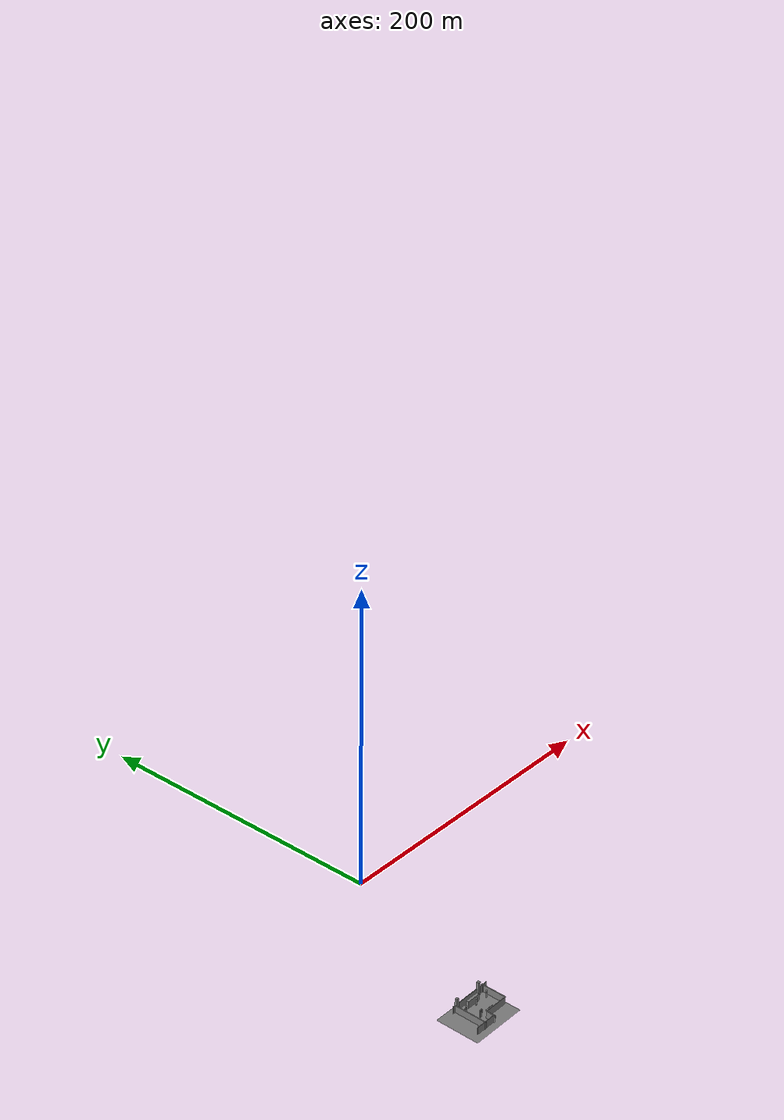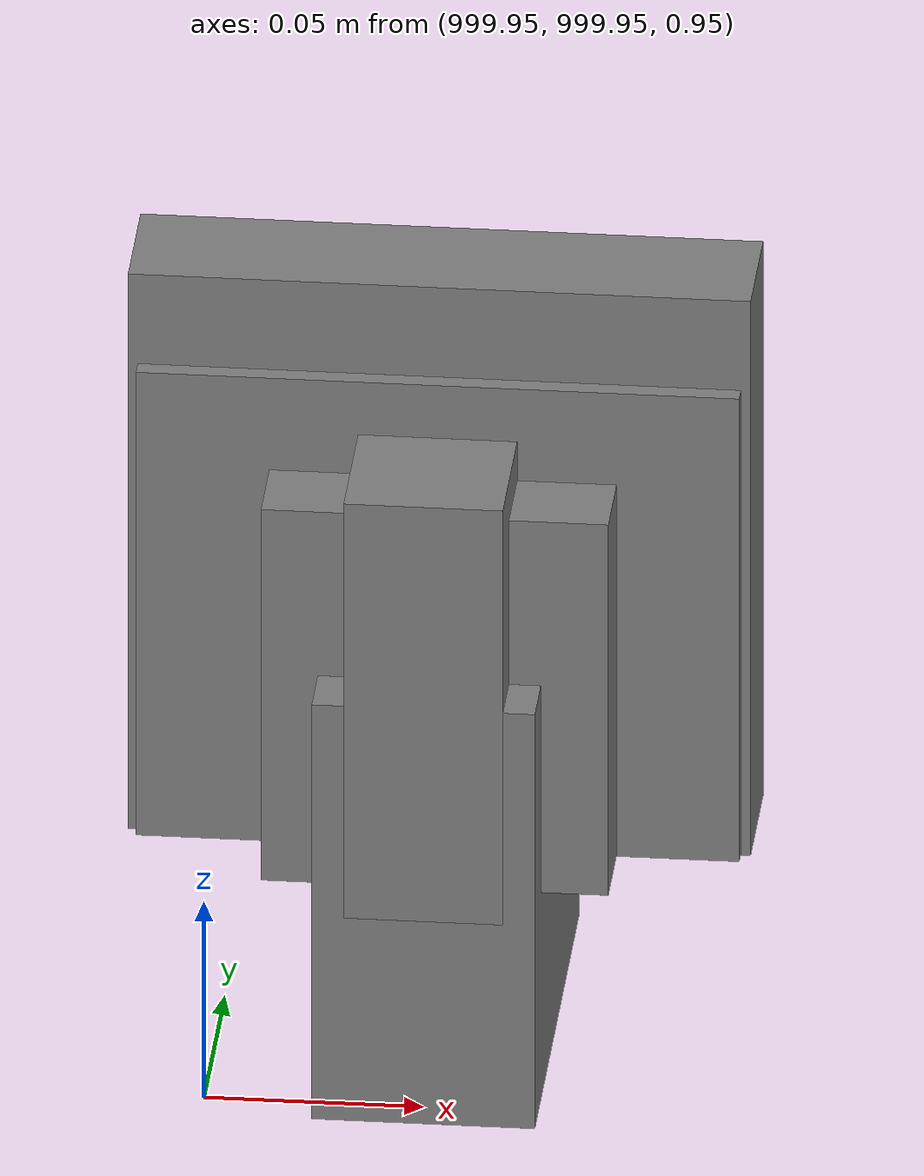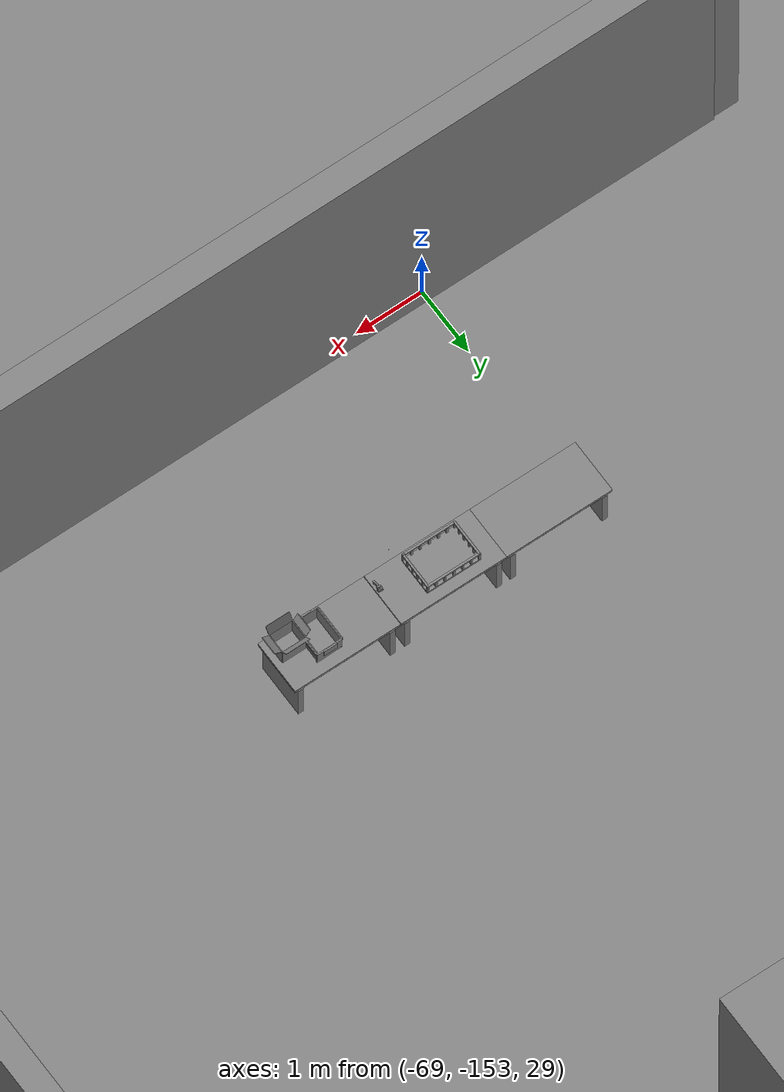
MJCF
<mujoco>
    <option gravity="0.000000000 0.000000000 -9.810000420" timestep="0.0049999999" integrator="implicitfast" density="1.225" viscosity="1.8000001e-05" noslip_iterations="10" iterations="100" sdf_iterations="50">
        <flag multiccd="disable"/>
    </option>
    <size memory="1000M"/>
    <compiler coordinate="local"/>
    <worldbody>
        <light cutoff="30" pos="0 1 1" dir="0 -1 -2"/>
        <light cutoff="30" pos="0 -1 1" dir="0 1 -2"/>
        <body pos="-64.866622925 -149.383972168 30.183746338" euler="89.999984741 89.999946594 0.000000000" name="openloong_gripper_2f85_fix_base_usda_bluebox_01">
            <geom contype="1" conaffinity="1" density="1000" type="box" material="" rgba="0.500000000 0.500000000 0.500000000 1.000000000" solimp="0.899999976 0.949999988 0.001000000" friction="1.000000000 0.005000000 0.000100000" solref="0.020000000 1.000000000" margin="0" condim="3" group="0" pos="0.276580811 0.187225342 0.000068665" quat="0.707106948 0.000077471 0.707106352 0.000077486" size="0.100000001 0.057999998 0.010000000" name="openloong_gripper_2f85_fix_base_usda_geom_BB97B560_8439_49A0_8E1B_9AC121044AA3"/>
            <geom contype="1" conaffinity="1" density="1000" type="box" material="" rgba="0.500000000 0.500000000 0.500000000 1.000000000" solimp="0.899999976 0.949999988 0.001000000" friction="1.000000000 0.005000000 0.000100000" solref="0.020000000 1.000000000" margin="0" condim="3" group="0" pos="0.000000000 0.002883911 0.000000000" quat="0.999999881 0.000000000 0.000000000 0.000000000" size="0.254000008 0.003000000 0.172000006" name="openloong_gripper_2f85_fix_base_usda_geom_9D2FFE67_583B_4D81_9896_D2167F5C550D"/>
            <geom contype="1" conaffinity="1" density="1000" type="box" material="" rgba="0.500000000 0.500000000 0.500000000 1.000000000" solimp="0.899999976 0.949999988 0.001000000" friction="1.000000000 0.005000000 0.000100000" solref="0.020000000 1.000000000" margin="0" condim="3" group="0" pos="0.000000000 0.124874115 0.173484802" quat="0.999796331 0.020176515 -0.000000015 0.000000030" size="0.259999990 0.119999997 0.007000000" name="openloong_gripper_2f85_fix_base_usda_geom_153BFD20_28F2_4C05_9835_70B73C627FA5"/>
            <geom contype="1" conaffinity="1" density="1000" type="box" material="" rgba="0.500000000 0.500000000 0.500000000 1.000000000" solimp="0.899999976 0.949999988 0.001000000" friction="1.000000000 0.005000000 0.000100000" solref="0.020000000 1.000000000" margin="0" condim="3" group="0" pos="0.000000000 0.124874115 -0.173469543" quat="0.999796331 -0.020176545 -0.000000015 0.000000000" size="0.259999990 0.119999997 0.007000000" name="openloong_gripper_2f85_fix_base_usda_geom_8AC6F82D_FF38_4DAC_86F3_025FAE9BFCF3"/>
            <geom contype="1" conaffinity="1" density="1000" type="box" material="" rgba="0.500000000 0.500000000 0.500000000 1.000000000" solimp="0.899999976 0.949999988 0.001000000" friction="1.000000000 0.005000000 0.000100000" solref="0.020000000 1.000000000" margin="0" condim="3" group="0" pos="0.000000000 0.214008331 0.188980103" quat="0.999912977 0.013176724 0.000000015 0.000000000" size="0.259999990 0.029999999 0.012500000" name="openloong_gripper_2f85_fix_base_usda_geom_5AEC41ED_A2E4_4A12_B916_5B0F84BA6F65"/>
            <geom contype="1" conaffinity="1" density="1000" type="box" material="" rgba="0.500000000 0.500000000 0.500000000 1.000000000" solimp="0.899999976 0.949999988 0.001000000" friction="1.000000000 0.005000000 0.000100000" solref="0.020000000 1.000000000" margin="0" condim="3" group="0" pos="-0.258361816 0.125289917 0.001876831" quat="0.702796936 -0.020792112 0.710783124 0.020769298" size="0.189999998 0.119999997 0.009000000" name="openloong_gripper_2f85_fix_base_usda_geom_74E7446F_1E35_4838_9287_DB18A87CEECA"/>
            <geom contype="1" conaffinity="1" density="1000" type="box" material="" rgba="0.500000000 0.500000000 0.500000000 1.000000000" solimp="0.899999976 0.949999988 0.001000000" friction="1.000000000 0.005000000 0.000100000" solref="0.020000000 1.000000000" margin="0" condim="3" group="0" pos="0.000000000 0.214008331 -0.188980103" quat="0.999912977 -0.013176769 0.000000030 0.000000015" size="0.259999990 0.029999999 0.012500000" name="openloong_gripper_2f85_fix_base_usda_geom_80F91972_80F4_4B9E_9B33_BC7B2A21C58B"/>
            <geom contype="1" conaffinity="1" density="1000" type="box" material="" rgba="0.500000000 0.500000000 0.500000000 1.000000000" solimp="0.899999976 0.949999988 0.001000000" friction="1.000000000 0.005000000 0.000100000" solref="0.020000000 1.000000000" margin="0" condim="3" group="0" pos="-0.276611328 0.187225342 0.000068665" quat="0.707106650 0.000077441 0.707106709 0.000077456" size="0.100000001 0.057999998 0.010000000" name="openloong_gripper_2f85_fix_base_usda_geom_43C0202A_5263_4F7F_B653_3B6620EDA4F6"/>
            <geom contype="1" conaffinity="1" density="1000" type="box" material="" rgba="0.500000000 0.500000000 0.500000000 1.000000000" solimp="0.899999976 0.949999988 0.001000000" friction="1.000000000 0.005000000 0.000100000" solref="0.020000000 1.000000000" margin="0" condim="3" group="0" pos="0.258331299 0.125289917 0.001876831" quat="0.702851415 0.018856421 0.710823774 -0.019329369" size="0.189999998 0.119999997 0.009000000" name="openloong_gripper_2f85_fix_base_usda_geom_2DCEA920_F598_4EE4_956E_089C6257C78B"/>
            <freejoint name="openloong_gripper_2f85_fix_base_usda_bluebox_01_joint"/>
            <site size="0.005000000 0.005000000 0.005000000" rgba="0.500000000 0.500000000 0.500000000 1.000000000" pos="0.000000000 0.000000000 0.000000000" quat="0.999961913 0.008726534 0.000000000 0.000000000" group="0" type="sphere" name="openloong_gripper_2f85_fix_base_usda_bluebox_01site"/>
        </body>
        <body pos="-64.496299744 -149.491867065 30.235729218" euler="0.000000000 0.000000000 89.999946594" name="openloong_gripper_2f85_fix_base_usda_cardboardbox_01">
            <geom contype="1" conaffinity="1" density="1000" type="box" material="" rgba="0.500000000 0.500000000 0.500000000 1.000000000" solimp="0.899999976 0.949999988 0.001000000" friction="1.000000000 0.005000000 0.000100000" solref="0.020000000 1.000000000" margin="0" condim="3" group="0" pos="-0.003166199 -0.004086494 0.005052090" quat="1.000000000 0.000000000 0.000000000 0.000000000" size="0.142499998 0.177500010 0.005000000" name="openloong_gripper_2f85_fix_base_usda_geom_F7CEE5AA_A651_43F4_88F0_8CD2A9113722"/>
            <geom contype="1" conaffinity="1" density="1000" type="box" material="" rgba="0.500000000 0.500000000 0.500000000 1.000000000" solimp="0.899999976 0.949999988 0.001000000" friction="1.000000000 0.005000000 0.000100000" solref="0.020000000 1.000000000" margin="0" condim="3" group="0" pos="-0.003166199 0.170316696 0.150570869" quat="1.000000000 0.000000000 0.000000000 0.000000000" size="0.142499998 0.005000000 0.149999991" name="openloong_gripper_2f85_fix_base_usda_geom_77950C5E_CD81_44B7_B6C7_40719627117E"/>
            <geom contype="1" conaffinity="1" density="1000" type="box" material="" rgba="0.500000000 0.500000000 0.500000000 1.000000000" solimp="0.899999976 0.949999988 0.001000000" friction="1.000000000 0.005000000 0.000100000" solref="0.020000000 1.000000000" margin="0" condim="3" group="0" pos="-0.147399902 -0.005307198 0.150570869" quat="1.000000000 0.000000000 0.000000000 0.000000000" size="0.005000000 0.177500010 0.149999991" name="openloong_gripper_2f85_fix_base_usda_geom_4E14A20D_8AFC_4923_9474_4E7BE8628D90"/>
            <geom contype="1" conaffinity="1" density="1000" type="box" material="" rgba="0.500000000 0.500000000 0.500000000 1.000000000" solimp="0.899999976 0.949999988 0.001000000" friction="1.000000000 0.005000000 0.000100000" solref="0.020000000 1.000000000" margin="0" condim="3" group="0" pos="0.140275955 -0.005307198 0.150570869" quat="1.000000000 0.000000000 0.000000000 0.000000000" size="0.005000000 0.177500010 0.149999991" name="openloong_gripper_2f85_fix_base_usda_geom_A3E229CC_487E_43B0_942A_0B37481DA591"/>
            <geom contype="1" conaffinity="1" density="1000" type="box" material="" rgba="0.500000000 0.500000000 0.500000000 1.000000000" solimp="0.899999976 0.949999988 0.001000000" friction="1.000000000 0.005000000 0.000100000" solref="0.020000000 1.000000000" margin="0" condim="3" group="0" pos="-0.003166199 -0.181550980 0.150570869" quat="1.000000000 0.000000000 0.000000000 0.000000000" size="0.142499998 0.005000000 0.149999991" name="openloong_gripper_2f85_fix_base_usda_geom_510A5B7A_E3BA_4339_B3EF_4906D0187F3F"/>
            <freejoint name="openloong_gripper_2f85_fix_base_usda_cardboardbox_01_joint"/>
            <site size="0.005000000 0.005000000 0.005000000" rgba="0.500000000 0.500000000 0.500000000 1.000000000" pos="0.000000000 0.000000000 0.000000000" quat="0.999961913 0.008726535 0.000000000 0.000000000" group="0" type="sphere" name="openloong_gripper_2f85_fix_base_usda_site_235DBF31_468E_4E44_A367_3CFBA01317D7"/>
            <body pos="0.139160156 -0.004048347 0.301930904" euler="-179.999954224 49.383502960 179.999954224" name="openloong_gripper_2f85_fix_base_usda_A1_006">
                <geom contype="1" conaffinity="1" density="1000" type="box" material="" rgba="0.500000000 0.500000000 0.500000000 1.000000000" solimp="0.899999976 0.949999988 0.001000000" friction="1.000000000 0.005000000 0.000100000" solref="0.020000000 1.000000000" margin="0" condim="3" group="0" pos="-0.071587563 0.000009537 0.001745224" quat="0.999999881 0.000000000 0.000000000 0.000000000" size="0.071249999 0.179999992 0.002500000" name="openloong_gripper_2f85_fix_base_usda_geom_4ED7CBC6_1A5C_4C2B_8DDD_57ED4FAB3392"/>
                <joint armature="0" stiffness="0.07" damping="0.0099999998" axis="0.000000 1.000000 0.000000" type="hinge" name="openloong_gripper_2f85_fix_base_usda_A1_006"/>
            </body>
            <body pos="-0.145902634 -0.004086494 0.301938057" euler="-180.000000000 -60.000011444 -180.000000000" name="openloong_gripper_2f85_fix_base_usda_A2_006">
                <geom contype="1" conaffinity="1" density="1000" type="box" material="" rgba="0.500000000 0.500000000 0.500000000 1.000000000" solimp="0.899999976 0.949999988 0.001000000" friction="1.000000000 0.005000000 0.000100000" solref="0.020000000 1.000000000" margin="0" condim="3" group="0" pos="0.071268082 0.000009537 0.002717972" quat="0.000002921 0.000000000 -0.000000030 0.999999881" size="0.071249999 0.179999992 0.002500000" name="openloong_gripper_2f85_fix_base_usda_geom_80F60343_FEC9_4CCC_8868_370CA341B0E0"/>
                <joint armature="0" stiffness="0.07" damping="0.0099999998" axis="0.000000 1.000000 0.000000" type="hinge" name="openloong_gripper_2f85_fix_base_usda_A2_006"/>
            </body>
            <body pos="-0.003385544 0.175991058 0.301930904" euler="-125.858116150 -0.000004561 0.000002331" name="openloong_gripper_2f85_fix_base_usda_B2_006">
                <geom contype="1" conaffinity="1" density="1000" type="box" material="" rgba="0.500000000 0.500000000 0.500000000 1.000000000" solimp="0.899999976 0.949999988 0.001000000" friction="1.000000000 0.005000000 0.000100000" solref="0.020000000 1.000000000" margin="0" condim="3" group="0" pos="0.000009537 -0.070939064 -0.002470016" quat="0.999614120 0.027776197 -0.000000015 0.000000030" size="0.137500003 0.064999998 0.005000000" name="openloong_gripper_2f85_fix_base_usda_geom_4FD37449_C874_4E75_A25E_856F5EE7D5EB"/>
                <joint armature="0" stiffness="0.07" damping="0.0099999998" axis="1.000000 0.000000 0.000000" type="hinge" name="openloong_gripper_2f85_fix_base_usda_B2_006"/>
            </body>
            <body pos="-0.003385544 -0.184140205 0.301938057" euler="147.805557251 0.000000000 0.000000000" name="openloong_gripper_2f85_fix_base_usda_B1_006">
                <geom contype="1" conaffinity="1" density="1000" type="box" material="" rgba="0.500000000 0.500000000 0.500000000 1.000000000" solimp="0.899999976 0.949999988 0.001000000" friction="1.000000000 0.005000000 0.000100000" solref="0.020000000 1.000000000" margin="0" condim="3" group="0" pos="-0.000028610 0.070202351 -0.002703667" quat="0.999614179 -0.027776167 0.000000000 0.000000000" size="0.137500003 0.064999998 0.005000000" name="openloong_gripper_2f85_fix_base_usda_geom_EB36A2FC_F13F_4F12_A52D_9319EABB503C"/>
                <joint armature="0" stiffness="0.07" damping="0.0099999998" axis="1.000000 0.000000 0.000000" type="hinge" name="openloong_gripper_2f85_fix_base_usda_B1_006"/>
            </body>
        </body>
        <body pos="-65.882858276 -149.481979370 30.229999542" euler="-64.487716675 0.000000000 0.000000000" name="openloong_gripper_2f85_fix_base_usda_Barcode">
            <geom contype="1" conaffinity="1" density="1000" type="box" material="" rgba="0.500000000 0.500000000 0.500000000 1.000000000" solimp="0.899999976 0.949999988 0.001000000" friction="1.000000000 0.005000000 0.000100000" solref="0.020000000 1.000000000" margin="0" condim="3" group="0" pos="0.000000000 0.013038635 0.001419067" quat="0.000000000 0.000000000 0.000000000 1.000000119" size="0.034000002 0.010000000 0.017999999" name="openloong_gripper_2f85_fix_base_usda_geom_363E49F3_DEB0_49B9_93A0_784CE9632D85"/>
            <geom contype="1" conaffinity="1" density="1000" type="box" material="" rgba="0.500000000 0.500000000 0.500000000 1.000000000" solimp="0.899999976 0.949999988 0.001000000" friction="1.000000000 0.005000000 0.000100000" solref="0.020000000 1.000000000" margin="0" condim="3" group="0" pos="0.000000000 -0.035301208 -0.007095337" quat="0.000000000 0.000000000 -0.043619365 0.999048233" size="0.028999999 0.010000000 0.020000000" name="openloong_gripper_2f85_fix_base_usda_geom_99D296A4_D86E_463F_882F_B2D7EFEF97E9"/>
            <geom contype="1" conaffinity="1" density="1000" type="box" material="" rgba="0.500000000 0.500000000 0.500000000 1.000000000" solimp="0.899999976 0.949999988 0.001000000" friction="1.000000000 0.005000000 0.000100000" solref="0.020000000 1.000000000" margin="0" condim="3" group="0" pos="0.000000000 -0.043411255 -0.011749268" quat="0.922262907 0.386563420 0.000000000 0.000000000" size="0.026000001 0.010000000 0.020000000" name="openloong_gripper_2f85_fix_base_usda_geom_59439B63_935B_419A_B6D2_6A6998930811"/>
            <geom contype="1" conaffinity="1" density="1000" type="box" material="" rgba="0.500000000 0.500000000 0.500000000 1.000000000" solimp="0.899999976 0.949999988 0.001000000" friction="1.000000000 0.005000000 0.000100000" solref="0.020000000 1.000000000" margin="0" condim="3" group="0" pos="0.000000000 -0.016967773 -0.031860352" quat="0.000000000 0.000000000 0.000000000 1.000000119" size="0.008000000 0.010000000 0.013000000" name="openloong_gripper_2f85_fix_base_usda_geom_A0B2485A_8D37_4395_81F8_652B043603E3"/>
            <geom contype="1" conaffinity="1" density="1000" type="box" material="" rgba="0.500000000 0.500000000 0.500000000 1.000000000" solimp="0.899999976 0.949999988 0.001000000" friction="1.000000000 0.005000000 0.000100000" solref="0.020000000 1.000000000" margin="0" condim="3" group="0" pos="0.000000000 -0.001869202 0.000312805" quat="0.953716993 0.300705761 0.000000000 0.000000000" size="0.032000002 0.010000000 0.018999999" name="openloong_gripper_2f85_fix_base_usda_geom_44A88035_D8CB_4AFC_AF76_CE3A7B79E0CD"/>
            <geom contype="1" conaffinity="1" density="1000" type="box" material="" rgba="0.500000000 0.500000000 0.500000000 1.000000000" solimp="0.899999976 0.949999988 0.001000000" friction="1.000000000 0.005000000 0.000100000" solref="0.020000000 1.000000000" margin="0" condim="3" group="0" pos="0.000000000 -0.019531250 -0.003173828" quat="0.953716993 0.300705761 0.000000000 0.000000000" size="0.030999999 0.010000000 0.020000000" name="openloong_gripper_2f85_fix_base_usda_geom_5D202B1C_D768_4EFE_B33A_F0A0A6E98429"/>
            <geom contype="1" conaffinity="1" density="1000" type="box" material="" rgba="0.500000000 0.500000000 0.500000000 1.000000000" solimp="0.899999976 0.949999988 0.001000000" friction="1.000000000 0.005000000 0.000100000" solref="0.020000000 1.000000000" margin="0" condim="3" group="0" pos="0.000000000 -0.035301208 -0.007095337" quat="0.953716993 0.300705761 0.000000000 0.000000000" size="0.028999999 0.010000000 0.020000000" name="openloong_gripper_2f85_fix_base_usda_geom_1CF5CC91_FBCF_4290_9095_B540744E6933"/>
            <geom contype="1" conaffinity="1" density="1000" type="box" material="" rgba="0.500000000 0.500000000 0.500000000 1.000000000" solimp="0.899999976 0.949999988 0.001000000" friction="1.000000000 0.005000000 0.000100000" solref="0.020000000 1.000000000" margin="0" condim="3" group="0" pos="0.000000000 -0.042617798 -0.071121216" quat="0.000000000 0.000000000 0.000000000 1.000000119" size="0.013000000 0.021000000 0.059999999" name="openloong_gripper_2f85_fix_base_usda_geom_06EAA745_1C3F_458B_9BED_11E8A241F968"/>
            <freejoint name="openloong_gripper_2f85_fix_base_usda_Barcode_joint"/>
            <site size="0.005000000 0.005000000 0.005000000" rgba="0.500000000 0.500000000 0.500000000 1.000000000" pos="0.000000000 0.000000000 0.000000000" quat="1.000000000 0.000000000 0.000000000 0.000000000" group="0" type="sphere" name="openloong_gripper_2f85_fix_base_usda_Barcode_site"/>
        </body>
        <body pos="-66.745018005 -149.392349243 30.184000015" euler="0.000000000 0.000000000 89.999946594" name="[22332756675878]_Basket_01">
            <geom contype="1" conaffinity="1" density="1000" type="box" material="" rgba="0.500000000 0.500000000 0.500000000 1.000000000" solimp="0.899999976 0.949999988 0.001000000" friction="1.000000000 0.005000000 0.000100000" solref="0.020000000 1.000000000" margin="0" condim="3" group="0" pos="-0.052425385 0.389207840 0.089787483" quat="0.707107008 0.000000000 0.000000000 0.707106411" size="0.014249999 0.014249999 0.059999999" name="[22332756675878]_geom_49C81EC8_6405_444D_A926_130602ADACD9"/>
            <geom contype="1" conaffinity="1" density="1000" type="box" material="" rgba="0.500000000 0.500000000 0.500000000 1.000000000" solimp="0.899999976 0.949999988 0.001000000" friction="1.000000000 0.005000000 0.000100000" solref="0.020000000 1.000000000" margin="0" condim="3" group="0" pos="0.264015198 -0.133043289 0.089787483" quat="0.707107008 0.000000000 0.000000000 0.707106411" size="0.014249999 0.014249999 0.059999999" name="[22332756675878]_geom_5A52A8E7_C2CC_446D_8456_B0443A86DE75"/>
            <geom contype="1" conaffinity="1" density="1000" type="box" material="" rgba="0.500000000 0.500000000 0.500000000 1.000000000" solimp="0.899999976 0.949999988 0.001000000" friction="1.000000000 0.005000000 0.000100000" solref="0.020000000 1.000000000" margin="0" condim="3" group="0" pos="-0.264015198 -0.265548706 0.089793205" quat="0.707107008 0.000000000 0.000000000 0.707106411" size="0.014249999 0.014249999 0.059999999" name="[22332756675878]_geom_86E346AE_6F38_4693_B85C_139177BA69AB"/>
            <geom contype="1" conaffinity="1" density="1000" type="box" material="" rgba="0.500000000 0.500000000 0.500000000 1.000000000" solimp="0.899999976 0.949999988 0.001000000" friction="1.000000000 0.005000000 0.000100000" solref="0.020000000 1.000000000" margin="0" condim="3" group="0" pos="-0.160263062 -0.389322281 0.089793205" quat="0.707107008 0.000000000 0.000000000 0.707106411" size="0.014249999 0.014249999 0.059999999" name="[22332756675878]_geom_45EA5D05_23B9_49DC_B8AE_380C7E08DEFD"/>
            <geom contype="1" conaffinity="1" density="1000" type="box" material="" rgba="0.500000000 0.500000000 0.500000000 1.000000000" solimp="0.899999976 0.949999988 0.001000000" friction="1.000000000 0.005000000 0.000100000" solref="0.020000000 1.000000000" margin="0" condim="3" group="0" pos="0.162265778 -0.389322281 0.089787483" quat="0.707107008 0.000000000 0.000000000 0.707106411" size="0.014249999 0.014249999 0.059999999" name="[22332756675878]_geom_A800437B_246E_4463_8587_5AE104ED6953"/>
            <geom contype="1" conaffinity="1" density="1000" type="box" material="" rgba="0.500000000 0.500000000 0.500000000 1.000000000" solimp="0.899999976 0.949999988 0.001000000" friction="1.000000000 0.005000000 0.000100000" solref="0.020000000 1.000000000" margin="0" condim="3" group="0" pos="0.264015198 0.389207840 0.089787483" quat="0.707107008 0.000000000 0.000000000 0.707106411" size="0.014249999 0.014249999 0.059999999" name="[22332756675878]_geom_6BC3E3FF_FF72_4348_A067_A02DE416810A"/>
            <geom contype="1" conaffinity="1" density="1000" type="box" material="" rgba="0.500000000 0.500000000 0.500000000 1.000000000" solimp="0.899999976 0.949999988 0.001000000" friction="1.000000000 0.005000000 0.000100000" solref="0.020000000 1.000000000" margin="0" condim="3" group="0" pos="-0.264015198 -0.133043289 0.089793205" quat="0.707107008 0.000000000 0.000000000 0.707106411" size="0.014249999 0.014249999 0.059999999" name="[22332756675878]_geom_AD7DEDB8_3124_4C06_8830_DCE81023E7E6"/>
            <geom contype="1" conaffinity="1" density="1000" type="box" material="" rgba="0.500000000 0.500000000 0.500000000 1.000000000" solimp="0.899999976 0.949999988 0.001000000" friction="1.000000000 0.005000000 0.000100000" solref="0.020000000 1.000000000" margin="0" condim="3" group="0" pos="-0.264026642 0.269256592 0.089793205" quat="0.707107008 0.000000000 0.000000000 0.707106411" size="0.014249999 0.014249999 0.059999999" name="[22332756675878]_geom_6331ECAC_A817_4C47_8C7D_349C377EB6E6"/>
            <geom contype="1" conaffinity="1" density="1000" type="box" material="" rgba="0.500000000 0.500000000 0.500000000 1.000000000" solimp="0.899999976 0.949999988 0.001000000" friction="1.000000000 0.005000000 0.000100000" solref="0.020000000 1.000000000" margin="0" condim="3" group="0" pos="0.054462433 0.389207840 0.089787483" quat="0.707107008 0.000000000 0.000000000 0.707106411" size="0.014249999 0.014249999 0.059999999" name="[22332756675878]_geom_B9B2B2B2_5266_41F4_976C_C8508C96B976"/>
            <geom contype="1" conaffinity="1" density="1000" type="box" material="" rgba="0.500000000 0.500000000 0.500000000 1.000000000" solimp="0.899999976 0.949999988 0.001000000" friction="1.000000000 0.005000000 0.000100000" solref="0.020000000 1.000000000" margin="0" condim="3" group="0" pos="0.054462433 -0.389322281 0.089787483" quat="0.707107008 0.000000000 0.000000000 0.707106411" size="0.014249999 0.014249999 0.059999999" name="[22332756675878]_geom_99C8E4CF_5DF6_473D_9487_83727029CA69"/>
            <geom contype="1" conaffinity="1" density="1000" type="box" material="" rgba="0.500000000 0.500000000 0.500000000 1.000000000" solimp="0.899999976 0.949999988 0.001000000" friction="1.000000000 0.005000000 0.000100000" solref="0.020000000 1.000000000" margin="0" condim="3" group="0" pos="0.264015198 0.269256592 0.089793205" quat="0.707107008 0.000000000 0.000000000 0.707106411" size="0.014249999 0.014249999 0.059999999" name="[22332756675878]_geom_E4F80FF0_7B06_4D80_BA1A_48D91BCE5E0F"/>
            <geom contype="1" conaffinity="1" density="1000" type="box" material="" rgba="0.500000000 0.500000000 0.500000000 1.000000000" solimp="0.899999976 0.949999988 0.001000000" friction="1.000000000 0.005000000 0.000100000" solref="0.020000000 1.000000000" margin="0" condim="3" group="0" pos="0.264015198 -0.389322281 0.089787483" quat="0.707107008 0.000000000 0.000000000 0.707106411" size="0.014249999 0.014249999 0.059999999" name="[22332756675878]_geom_577326BA_50C3_47DE_B898_E20DC80A474C"/>
            <geom contype="1" conaffinity="1" density="1000" type="box" material="" rgba="0.500000000 0.500000000 0.500000000 1.000000000" solimp="0.899999976 0.949999988 0.001000000" friction="1.000000000 0.005000000 0.000100000" solref="0.020000000 1.000000000" margin="0" condim="3" group="0" pos="0.000000000 0.000000000 0.015998840" quat="0.707107008 0.000000000 0.000000000 0.707106411" size="0.403499991 0.279000014 0.015750000" name="[22332756675878]_geom_77D870BC_858D_4B02_A38B_96ADAD63ACE2"/>
            <geom contype="1" conaffinity="1" density="1000" type="box" material="" rgba="0.500000000 0.500000000 0.500000000 1.000000000" solimp="0.899999976 0.949999988 0.001000000" friction="1.000000000 0.005000000 0.000100000" solref="0.020000000 1.000000000" margin="0" condim="3" group="0" pos="0.000000000 -0.389476776 0.163619041" quat="0.707107008 0.000000000 0.000000000 0.707106411" size="0.015000000 0.277500004 0.015750000" name="[22332756675878]_geom_2D3D2BC0_81AA_40D8_8885_9DE6CD716096"/>
            <geom contype="1" conaffinity="1" density="1000" type="box" material="" rgba="0.500000000 0.500000000 0.500000000 1.000000000" solimp="0.899999976 0.949999988 0.001000000" friction="1.000000000 0.005000000 0.000100000" solref="0.020000000 1.000000000" margin="0" condim="3" group="0" pos="0.162265778 0.389207840 0.089787483" quat="0.707107008 0.000000000 0.000000000 0.707106411" size="0.014249999 0.014249999 0.059999999" name="[22332756675878]_geom_0BF025A8_881A_4AA0_8981_8D2D68B210F7"/>
            <geom contype="1" conaffinity="1" density="1000" type="box" material="" rgba="0.500000000 0.500000000 0.500000000 1.000000000" solimp="0.899999976 0.949999988 0.001000000" friction="1.000000000 0.005000000 0.000100000" solref="0.020000000 1.000000000" margin="0" condim="3" group="0" pos="0.000000000 0.389471054 0.163619041" quat="0.707107008 0.000000000 0.000000000 0.707106411" size="0.015000000 0.277500004 0.015750000" name="[22332756675878]_geom_17B0F1EF_81F3_4FDC_8351_B34C188E3605"/>
            <geom contype="1" conaffinity="1" density="1000" type="box" material="" rgba="0.500000000 0.500000000 0.500000000 1.000000000" solimp="0.899999976 0.949999988 0.001000000" friction="1.000000000 0.005000000 0.000100000" solref="0.020000000 1.000000000" margin="0" condim="3" group="0" pos="-0.263511658 0.000000000 0.163619041" quat="0.707107008 0.000000000 0.000000000 0.707106411" size="0.403499991 0.015000000 0.015750000" name="[22332756675878]_geom_C3332427_02B6_4E95_9E76_150C5973723E"/>
            <geom contype="1" conaffinity="1" density="1000" type="box" material="" rgba="0.500000000 0.500000000 0.500000000 1.000000000" solimp="0.899999976 0.949999988 0.001000000" friction="1.000000000 0.005000000 0.000100000" solref="0.020000000 1.000000000" margin="0" condim="3" group="0" pos="-0.264015198 0.141334534 0.089793205" quat="0.707107008 0.000000000 0.000000000 0.707106411" size="0.014249999 0.014249999 0.059999999" name="[22332756675878]_geom_E01AC654_D3A8_4E5F_9F7C_2C4BFFCC56A4"/>
            <geom contype="1" conaffinity="1" density="1000" type="box" material="" rgba="0.500000000 0.500000000 0.500000000 1.000000000" solimp="0.899999976 0.949999988 0.001000000" friction="1.000000000 0.005000000 0.000100000" solref="0.020000000 1.000000000" margin="0" condim="3" group="0" pos="0.264015198 -0.265548706 0.089787483" quat="0.707107008 0.000000000 0.000000000 0.707106411" size="0.014249999 0.014249999 0.059999999" name="[22332756675878]_geom_ADF31347_26B4_4745_AF13_6CD78C085455"/>
            <geom contype="1" conaffinity="1" density="1000" type="box" material="" rgba="0.500000000 0.500000000 0.500000000 1.000000000" solimp="0.899999976 0.949999988 0.001000000" friction="1.000000000 0.005000000 0.000100000" solref="0.020000000 1.000000000" margin="0" condim="3" group="0" pos="-0.160263062 0.389207840 0.089787483" quat="0.707107008 0.000000000 0.000000000 0.707106411" size="0.014249999 0.014249999 0.059999999" name="[22332756675878]_geom_9AA2F0C0_F122_45B3_8883_2891116D4ACF"/>
            <geom contype="1" conaffinity="1" density="1000" type="box" material="" rgba="0.500000000 0.500000000 0.500000000 1.000000000" solimp="0.899999976 0.949999988 0.001000000" friction="1.000000000 0.005000000 0.000100000" solref="0.020000000 1.000000000" margin="0" condim="3" group="0" pos="-0.052425385 -0.389322281 0.089787483" quat="0.707107008 0.000000000 0.000000000 0.707106411" size="0.014249999 0.014249999 0.059999999" name="[22332756675878]_geom_D65B6877_A383_42F9_B57B_935C52F49F34"/>
            <geom contype="1" conaffinity="1" density="1000" type="box" material="" rgba="0.500000000 0.500000000 0.500000000 1.000000000" solimp="0.899999976 0.949999988 0.001000000" friction="1.000000000 0.005000000 0.000100000" solref="0.020000000 1.000000000" margin="0" condim="3" group="0" pos="-0.264026642 -0.389322281 0.089793205" quat="0.707107008 0.000000000 0.000000000 0.707106411" size="0.014249999 0.014249999 0.059999999" name="[22332756675878]_geom_7A395920_221E_488B_B69E_B3BE1246C076"/>
            <geom contype="1" conaffinity="1" density="1000" type="box" material="" rgba="0.500000000 0.500000000 0.500000000 1.000000000" solimp="0.899999976 0.949999988 0.001000000" friction="1.000000000 0.005000000 0.000100000" solref="0.020000000 1.000000000" margin="0" condim="3" group="0" pos="0.264015198 0.141334534 0.089787483" quat="0.707107008 0.000000000 0.000000000 0.707106411" size="0.014249999 0.014249999 0.059999999" name="[22332756675878]_geom_4157B687_50CC_4DA4_AC70_8646A511D3A8"/>
            <geom contype="1" conaffinity="1" density="1000" type="box" material="" rgba="0.500000000 0.500000000 0.500000000 1.000000000" solimp="0.899999976 0.949999988 0.001000000" friction="1.000000000 0.005000000 0.000100000" solref="0.020000000 1.000000000" margin="0" condim="3" group="0" pos="-0.264015198 0.389207840 0.089793205" quat="0.707107008 0.000000000 0.000000000 0.707106411" size="0.014249999 0.014249999 0.059999999" name="[22332756675878]_geom_EBC2A6D6_27C8_4F63_8D42_0A537149256C"/>
            <geom contype="1" conaffinity="1" density="1000" type="box" material="" rgba="0.500000000 0.500000000 0.500000000 1.000000000" solimp="0.899999976 0.949999988 0.001000000" friction="1.000000000 0.005000000 0.000100000" solref="0.020000000 1.000000000" margin="0" condim="3" group="0" pos="0.264015198 0.004480362 0.089787483" quat="0.707107008 0.000000000 0.000000000 0.707106411" size="0.014249999 0.014249999 0.059999999" name="[22332756675878]_geom_0209CB9D_1F29_47C7_9B37_752A9C389CC9"/>
            <geom contype="1" conaffinity="1" density="1000" type="box" material="" rgba="0.500000000 0.500000000 0.500000000 1.000000000" solimp="0.899999976 0.949999988 0.001000000" friction="1.000000000 0.005000000 0.000100000" solref="0.020000000 1.000000000" margin="0" condim="3" group="0" pos="0.263694763 -0.000011444 0.163619041" quat="0.707107008 0.000000000 0.000000000 0.707106411" size="0.403499991 0.015000000 0.015750000" name="[22332756675878]_geom_B2FF3708_146B_4B95_9152_A71E9340816C"/>
            <geom contype="1" conaffinity="1" density="1000" type="box" material="" rgba="0.500000000 0.500000000 0.500000000 1.000000000" solimp="0.899999976 0.949999988 0.001000000" friction="1.000000000 0.005000000 0.000100000" solref="0.020000000 1.000000000" margin="0" condim="3" group="0" pos="-0.264015198 0.004480362 0.089793205" quat="0.707107008 0.000000000 0.000000000 0.707106411" size="0.014249999 0.014249999 0.059999999" name="[22332756675878]_geom_F0E20610_ECDA_412F_A3E9_AE0391CC1E11"/>
            <freejoint name="[22332756675878]_joint_6C05BD3A_5D5E_4F5B_80E2_E0AC30F70F37"/>
        </body>
        <body pos="0.000000000 0.000000000 0.000000000" euler="0.000000000 0.000000000 0.000000000" name="Static Objects_Static Objects">
            <geom contype="1" conaffinity="1" density="1000" type="box" material="" rgba="0.500000000 0.500000000 0.500000000 1.000000000" solimp="0.899999976 0.949999988 0.001000000" friction="1.000000000 0.005000000 0.000100000" solref="0.020000000 1.000000000" margin="0" condim="3" group="0" pos="-67.544113159 -149.365814209 29.727830887" quat="0.500000417 0.499999970 0.499999553 0.499999970" size="0.381000012 0.319999993 0.041000001" name="Static Objects_geom_4A0A720D_0802_4CDE_BD7B_D3935E308953"/>
            <geom contype="1" conaffinity="1" density="1000" type="box" material="" rgba="0.500000000 0.500000000 0.500000000 1.000000000" solimp="0.899999976 0.949999988 0.001000000" friction="1.000000000 0.005000000 0.000100000" solref="0.020000000 1.000000000" margin="0" condim="3" group="0" pos="-68.239501953 -149.365814209 30.086868286" quat="0.500000417 0.499999970 0.499999553 0.499999970" size="0.370999992 0.039500002 0.745000005" name="Static Objects_geom_836D9419_FE0E_495B_B943_62BF027DDC5F"/>
            <geom contype="1" conaffinity="1" density="1000" type="box" material="" rgba="0.500000000 0.500000000 0.500000000 1.000000000" solimp="0.899999976 0.949999988 0.001000000" friction="1.000000000 0.005000000 0.000100000" solref="0.020000000 1.000000000" margin="0" condim="3" group="0" pos="-68.239501953 -149.365814209 30.147235870" quat="0.500000417 0.499999970 0.499999553 0.499999970" size="0.400000006 0.022000000 0.800000012" name="Static Objects_geom_96237E63_419D_489C_AB72_81522968741B"/>
            <geom contype="1" conaffinity="1" density="1000" type="box" material="" rgba="0.500000000 0.500000000 0.500000000 1.000000000" solimp="0.899999976 0.949999988 0.001000000" friction="1.000000000 0.005000000 0.000100000" solref="0.020000000 1.000000000" margin="0" condim="3" group="0" pos="-68.934890747 -149.365814209 29.727830887" quat="0.500000417 0.499999970 0.499999553 0.499999970" size="0.381000012 0.319999993 0.041000001" name="Static Objects_geom_AC4F8BDB_6C8C_48E5_82D8_07BBA9B56805"/>
            <geom contype="1" conaffinity="1" density="1000" type="box" material="" rgba="0.500000000 0.500000000 0.500000000 1.000000000" solimp="0.899999976 0.949999988 0.001000000" friction="1.000000000 0.005000000 0.000100000" solref="0.020000000 1.000000000" margin="0" condim="3" group="0" pos="-68.239501953 -149.365814209 29.561563492" quat="0.500000417 0.499999970 0.499999553 0.499999970" size="0.020000000 0.022000000 0.660000026" name="Static Objects_geom_BB2C10FD_0BB3_4DE1_ADE0_8C83419E0334"/>
            <geom contype="1" conaffinity="1" density="1000" type="box" material="" rgba="0.500000000 0.500000000 0.500000000 1.000000000" solimp="0.899999976 0.949999988 0.001000000" friction="1.000000000 0.005000000 0.000100000" solref="0.020000000 1.000000000" margin="0" condim="3" group="0" pos="-65.945671082 -149.365814209 29.727830887" quat="0.500000417 0.499999970 0.499999553 0.499999970" size="0.381000012 0.319999993 0.041000001" name="Static Objects_geom_CAB37E6E_3A34_479D_B268_0A31D7EF3B28"/>
            <geom contype="1" conaffinity="1" density="1000" type="box" material="" rgba="0.500000000 0.500000000 0.500000000 1.000000000" solimp="0.899999976 0.949999988 0.001000000" friction="1.000000000 0.005000000 0.000100000" solref="0.020000000 1.000000000" margin="0" condim="3" group="0" pos="-66.641059875 -149.365814209 30.086868286" quat="0.500000417 0.499999970 0.499999553 0.499999970" size="0.370999992 0.039500002 0.745000005" name="Static Objects_geom_CD5ED345_C192_4AB5_A04D_2118FFA70AE1"/>
            <geom contype="1" conaffinity="1" density="1000" type="box" material="" rgba="0.500000000 0.500000000 0.500000000 1.000000000" solimp="0.899999976 0.949999988 0.001000000" friction="1.000000000 0.005000000 0.000100000" solref="0.020000000 1.000000000" margin="0" condim="3" group="0" pos="-66.641059875 -149.365814209 30.147235870" quat="0.500000417 0.499999970 0.499999553 0.499999970" size="0.400000006 0.022000000 0.800000012" name="Static Objects_geom_AE213269_42F6_4967_A74B_2F18ACA79B02"/>
            <geom contype="1" conaffinity="1" density="1000" type="box" material="" rgba="0.500000000 0.500000000 0.500000000 1.000000000" solimp="0.899999976 0.949999988 0.001000000" friction="1.000000000 0.005000000 0.000100000" solref="0.020000000 1.000000000" margin="0" condim="3" group="0" pos="-67.336448669 -149.365814209 29.727830887" quat="0.500000417 0.499999970 0.499999553 0.499999970" size="0.381000012 0.319999993 0.041000001" name="Static Objects_geom_4F7AB2D6_543F_49D1_87FE_5D58EEBCDD5C"/>
            <geom contype="1" conaffinity="1" density="1000" type="box" material="" rgba="0.500000000 0.500000000 0.500000000 1.000000000" solimp="0.899999976 0.949999988 0.001000000" friction="1.000000000 0.005000000 0.000100000" solref="0.020000000 1.000000000" margin="0" condim="3" group="0" pos="-66.641059875 -149.365814209 29.561563492" quat="0.500000417 0.499999970 0.499999553 0.499999970" size="0.020000000 0.022000000 0.660000026" name="Static Objects_geom_BC6E174A_520B_4D41_A2DA_9F6B1A287F3D"/>
            <geom contype="1" conaffinity="1" density="1000" type="box" material="" rgba="0.500000000 0.500000000 0.500000000 1.000000000" solimp="0.899999976 0.949999988 0.001000000" friction="1.000000000 0.005000000 0.000100000" solref="0.020000000 1.000000000" margin="0" condim="3" group="0" pos="-64.338577271 -149.365814209 29.727830887" quat="0.500000417 0.499999970 0.499999553 0.499999970" size="0.381000012 0.319999993 0.041000001" name="Static Objects_geom_E291EA20_6BBB_4B12_AD91_67098536F338"/>
            <geom contype="1" conaffinity="1" density="1000" type="box" material="" rgba="0.500000000 0.500000000 0.500000000 1.000000000" solimp="0.899999976 0.949999988 0.001000000" friction="1.000000000 0.005000000 0.000100000" solref="0.020000000 1.000000000" margin="0" condim="3" group="0" pos="-65.033966064 -149.365814209 30.086868286" quat="0.500000417 0.499999970 0.499999553 0.499999970" size="0.370999992 0.039500002 0.745000005" name="Static Objects_geom_88715153_8D58_441B_95B8_99C139A3BB5E"/>
            <geom contype="1" conaffinity="1" density="1000" type="box" material="" rgba="0.500000000 0.500000000 0.500000000 1.000000000" solimp="0.899999976 0.949999988 0.001000000" friction="1.000000000 0.005000000 0.000100000" solref="0.020000000 1.000000000" margin="0" condim="3" group="0" pos="-65.033966064 -149.365814209 30.147235870" quat="0.500000417 0.499999970 0.499999553 0.499999970" size="0.400000006 0.022000000 0.800000012" name="Static Objects_geom_FB809BB4_D3FA_4077_8947_71DE1655B494"/>
            <geom contype="1" conaffinity="1" density="1000" type="box" material="" rgba="0.500000000 0.500000000 0.500000000 1.000000000" solimp="0.899999976 0.949999988 0.001000000" friction="1.000000000 0.005000000 0.000100000" solref="0.020000000 1.000000000" margin="0" condim="3" group="0" pos="-65.729354858 -149.365814209 29.727830887" quat="0.500000417 0.499999970 0.499999553 0.499999970" size="0.381000012 0.319999993 0.041000001" name="Static Objects_geom_FA92679C_B25A_4136_8D04_1905E973EEDC"/>
            <geom contype="1" conaffinity="1" density="1000" type="box" material="" rgba="0.500000000 0.500000000 0.500000000 1.000000000" solimp="0.899999976 0.949999988 0.001000000" friction="1.000000000 0.005000000 0.000100000" solref="0.020000000 1.000000000" margin="0" condim="3" group="0" pos="-65.033966064 -149.365814209 29.561563492" quat="0.500000417 0.499999970 0.499999553 0.499999970" size="0.020000000 0.022000000 0.660000026" name="Static Objects_geom_CEF7524F_F6FC_43BA_828E_33F7197CAB1F"/>
            <geom contype="1" conaffinity="1" density="1000" type="box" material="" rgba="0.500000000 0.500000000 0.500000000 1.000000000" solimp="0.899999976 0.949999988 0.001000000" friction="1.000000000 0.005000000 0.000100000" solref="0.020000000 1.000000000" margin="0" condim="3" group="0" pos="-61.754566193 -137.853729248 33.906845093" quat="0.707107067 0.000000000 0.000000000 0.707106471" size="0.759999990 0.759999990 4.500000000" name="Static Objects_geom_E9143FCF_4225_4EE0_84AA_DE99CA3E42AA"/>
            <geom contype="1" conaffinity="1" density="1000" type="box" material="" rgba="0.500000000 0.500000000 0.500000000 1.000000000" solimp="0.899999976 0.949999988 0.001000000" friction="1.000000000 0.005000000 0.000100000" solref="0.020000000 1.000000000" margin="0" condim="3" group="0" pos="-57.511135101 -144.927108765 31.707921982" quat="1.000000000 0.000000000 0.000000000 0.000000000" size="0.200000003 8.000000000 2.299999952" name="Static Objects_geom_2C49CF31_C376_46A5_9E81_E7E3F41BC557"/>
            <geom contype="1" conaffinity="1" density="1000" type="box" material="" rgba="0.500000000 0.500000000 0.500000000 1.000000000" solimp="0.899999976 0.949999988 0.001000000" friction="1.000000000 0.005000000 0.000100000" solref="0.020000000 1.000000000" margin="0" condim="3" group="0" pos="-80.517646790 -157.574050903 31.688196182" quat="0.707107067 0.000000000 0.000000000 0.707106471" size="0.600000024 0.600000024 2.299999952" name="Static Objects_geom_06D5D8CA_3619_463D_90F0_0E14CE21ECDA"/>
            <geom contype="1" conaffinity="1" density="1000" type="box" material="" rgba="0.500000000 0.500000000 0.500000000 1.000000000" solimp="0.899999976 0.949999988 0.001000000" friction="1.000000000 0.005000000 0.000100000" solref="0.020000000 1.000000000" margin="0" condim="3" group="0" pos="-80.711044312 -147.414932251 31.666158676" quat="1.000000000 0.000000000 0.000000000 0.000000000" size="0.200000003 10.000000000 2.299999952" name="Static Objects_geom_2D40B6CF_E530_47AA_A3FE_64EA57FC9BE6"/>
            <geom contype="1" conaffinity="1" density="1000" type="box" material="" rgba="0.500000000 0.500000000 0.500000000 1.000000000" solimp="0.899999976 0.949999988 0.001000000" friction="1.000000000 0.005000000 0.000100000" solref="0.020000000 1.000000000" margin="0" condim="3" group="0" pos="-57.687217712 -137.434692383 31.688196182" quat="0.707107067 0.000000000 0.000000000 0.707106471" size="0.600000024 0.600000024 2.299999952" name="Static Objects_geom_0E0FE871_F3E4_4678_A27D_25819FAD1183"/>
            <geom contype="1" conaffinity="1" density="1000" type="box" material="" rgba="0.500000000 0.500000000 0.500000000 1.000000000" solimp="0.899999976 0.949999988 0.001000000" friction="1.000000000 0.005000000 0.000100000" solref="0.020000000 1.000000000" margin="0" condim="3" group="0" pos="-69.537033081 -140.263229370 31.714921951" quat="0.707107067 0.000000000 0.000000000 0.707106471" size="0.759999990 4.500000000 2.299999952" name="Static Objects_geom_D36C39EF_2267_4E9A_B2BD_33EACB277809"/>
            <geom contype="1" conaffinity="1" density="1000" type="box" material="" rgba="0.500000000 0.500000000 0.500000000 1.000000000" solimp="0.899999976 0.949999988 0.001000000" friction="1.000000000 0.005000000 0.000100000" solref="0.020000000 1.000000000" margin="0" condim="3" group="0" pos="-80.073638916 -137.853713989 33.906845093" quat="0.707107067 0.000000000 0.000000000 0.707106471" size="0.759999990 0.759999990 4.500000000" name="Static Objects_geom_451B4FC9_07D6_43C9_8886_D549433A1618"/>
            <geom contype="1" conaffinity="1" density="1000" type="box" material="" rgba="0.500000000 0.500000000 0.500000000 1.000000000" solimp="0.899999976 0.949999988 0.001000000" friction="1.000000000 0.005000000 0.000100000" solref="0.020000000 1.000000000" margin="0" condim="3" group="0" pos="-73.406707764 -155.734664917 31.707921982" quat="1.000000000 0.000000000 0.000000000 0.000000000" size="0.200000003 3.000000000 2.299999952" name="Static Objects_geom_BAFCD163_AC16_4BC6_A840_E186F9EBE830"/>
            <geom contype="1" conaffinity="1" density="1000" type="box" material="" rgba="0.500000000 0.500000000 0.500000000 1.000000000" solimp="0.899999976 0.949999988 0.001000000" friction="1.000000000 0.005000000 0.000100000" solref="0.020000000 1.000000000" margin="0" condim="3" group="0" pos="-68.497543335 -137.448257446 31.707921982" quat="0.707107067 0.000000000 0.000000000 0.707106471" size="0.200000003 14.000000000 2.299999952" name="Static Objects_geom_DB707BF5_EE28_46BE_8CFB_4CA0DA12EC40"/>
            <geom contype="1" conaffinity="1" density="1000" type="cylinder" material="" rgba="0.500000000 0.500000000 0.500000000 1.000000000" solimp="0.899999976 0.949999988 0.001000000" friction="1.000000000 0.005000000 0.000100000" solref="0.020000000 1.000000000" margin="0" condim="3" group="0" pos="-68.868522644 -142.134506226 31.711090088" quat="0.707107067 0.000000000 0.000000000 0.707106471" size="0.509999990 2.299999952 1.000000000" name="Static Objects_geom_FFAA1D07_0891_4BD6_9326_142FA0A10BDB"/>
            <geom contype="1" conaffinity="1" density="1000" type="plane" material="" rgba="0.500000000 0.500000000 0.500000000 1.000000000" solimp="0.899999976 0.949999988 0.001000000" friction="1.000000000 0.005000000 0.000100000" solref="0.020000000 1.000000000" margin="0" condim="3" group="0" pos="-72.873703003 -147.131927490 29.409669876" quat="1.000000000 0.000000000 0.000000000 0.000000000" size="18.000000000 14.000000000 1.000000000" name="Static Objects_geom_8F8C893F_917C_41C7_B289_7153444976DA"/>
            <geom contype="1" conaffinity="1" density="1000" type="box" material="" rgba="0.500000000 0.500000000 0.500000000 1.000000000" solimp="0.899999976 0.949999988 0.001000000" friction="1.000000000 0.005000000 0.000100000" solref="0.020000000 1.000000000" margin="0" condim="3" group="0" pos="-79.943580627 -157.782272339 31.707921982" quat="0.707107067 0.000000000 0.000000000 0.707106471" size="0.200000003 7.000000000 2.299999952" name="Static Objects_geom_034B29FA_41A3_4228_A430_4537CF954E78"/>
            <geom contype="1" conaffinity="1" density="1000" type="box" material="" rgba="0.500000000 0.500000000 0.500000000 1.000000000" solimp="0.899999976 0.949999988 0.001000000" friction="1.000000000 0.005000000 0.000100000" solref="0.020000000 1.000000000" margin="0" condim="3" group="0" pos="-65.421028137 -152.903442383 31.707921982" quat="0.707107067 0.000000000 0.000000000 0.707106471" size="0.200000003 7.800000191 2.299999952" name="Static Objects_geom_1CD1459E_1463_46C7_8FB7_D01F04C5ECE1"/>
            <geom contype="1" conaffinity="1" density="1000" type="box" material="" rgba="0.500000000 0.500000000 0.500000000 1.000000000" solimp="0.899999976 0.949999988 0.001000000" friction="1.000000000 0.005000000 0.000100000" solref="0.020000000 1.000000000" margin="0" condim="3" group="0" pos="-74.776908875 -149.964416504 31.688196182" quat="1.000000000 0.000000000 0.000000000 0.000000000" size="0.600000024 0.409999996 2.299999952" name="Static Objects_geom_1B7E2E5E_4118_4AF7_B9AA_F6C589BB218A"/>
            <geom contype="1" conaffinity="1" density="1000" type="cylinder" material="" rgba="0.500000000 0.500000000 0.500000000 1.000000000" solimp="0.899999976 0.949999988 0.001000000" friction="1.000000000 0.005000000 0.000100000" solref="0.020000000 1.000000000" margin="0" condim="3" group="0" pos="-60.161884308 -142.134506226 31.711090088" quat="0.707107067 0.000000000 0.000000000 0.707106471" size="0.509999990 2.299999952 1.000000000" name="Static Objects_geom_964E997E_79AB_4399_B2C9_4008F5F0A2A3"/>
            <geom contype="1" conaffinity="1" density="1000" type="cylinder" material="" rgba="0.500000000 0.500000000 0.500000000 1.000000000" solimp="0.899999976 0.949999988 0.001000000" friction="1.000000000 0.005000000 0.000100000" solref="0.020000000 1.000000000" margin="0" condim="3" group="0" pos="-75.382453918 -149.963455200 31.711090088" quat="0.707107067 0.000000000 0.000000000 0.707106471" size="0.409999996 2.299999952 1.000000000" name="Static Objects_geom_40B7191A_6DA1_4EA7_B223_0DC54EB06B73"/>
            <geom contype="1" conaffinity="1" density="1000" type="cylinder" material="" rgba="0.500000000 0.500000000 0.500000000 1.000000000" solimp="0.899999976 0.949999988 0.001000000" friction="1.000000000 0.005000000 0.000100000" solref="0.020000000 1.000000000" margin="0" condim="3" group="0" pos="-74.154960632 -149.963455200 31.711090088" quat="0.707107067 0.000000000 0.000000000 0.707106471" size="0.409999996 2.299999952 1.000000000" name="Static Objects_geom_D15FE073_AD20_4AAD_B0AC_0ED72A5D70EF"/>
            <geom contype="1" conaffinity="1" density="1000" type="cylinder" material="" rgba="0.500000000 0.500000000 0.500000000 1.000000000" solimp="0.899999976 0.949999988 0.001000000" friction="1.000000000 0.005000000 0.000100000" solref="0.020000000 1.000000000" margin="0" condim="3" group="0" pos="-77.566612244 -142.134506226 31.711090088" quat="0.707107067 0.000000000 0.000000000 0.707106471" size="0.509999990 2.299999952 1.000000000" name="Static Objects_geom_C76232C9_25D1_47AF_A51D_D16D5DE063EA"/>
        </body>
        <body pos="1000.000000000 1000.000000000 1.000000000" euler="0.000000000 0.000000000 180.000000000" name="openloong_gripper_2f85_fix_base_usda_wifi_box">
            <geom contype="1" conaffinity="1" density="1000" type="box" material="" rgba="0.500000000 0.500000000 0.500000000 1.000000000" solimp="0.899999976 0.949999988 0.001000000" friction="1.000000000 0.005000000 0.000100000" solref="0.020000000 1.000000000" margin="0" condim="3" group="0" pos="0.000000000 0.000000000 0.058978677" quat="0.000000000 0.000000047 0.000000000 1.000000000" size="0.068499997 0.018999999 0.059000000" name="openloong_gripper_2f85_fix_base_usda_geom_4C290588_21F3_4A54_B0E9_1B0283AE8B28"/>
            <freejoint name="openloong_gripper_2f85_fix_base_usda_wifi_box_joint"/>
            <site size="0.005000000 0.005000000 0.005000000" rgba="0.500000000 0.500000000 0.500000000 1.000000000" pos="0.000000000 0.000000000 0.000000000" quat="0.999961913 0.008726500 0.000000000 0.000000000" group="0" type="sphere" name="openloong_gripper_2f85_fix_base_usda_wifi_boxsite"/>
        </body>
        <body pos="-66.105720520 -149.381759644 31.164129257" euler="-92.746109009 -47.438732147 -175.154922485" mocap="true" name="spotlight6_SpotLight"/>
        <body pos="1000.000000000 1000.000000000 1.000000000" euler="0.000000000 0.000000000 180.000000000" name="openloong_gripper_2f85_fix_base_usda_cpu_fan">
            <geom contype="1" conaffinity="1" density="1000" type="box" material="" rgba="0.500000000 0.500000000 0.500000000 1.000000000" solimp="0.899999976 0.949999988 0.001000000" friction="1.000000000 0.005000000 0.000100000" solref="0.020000000 1.000000000" margin="0" condim="3" group="0" pos="0.000000000 0.000000000 0.070034981" quat="0.000000000 0.000000000 0.000000000 1.000000000" size="0.070700005 0.014699999 0.070700005" name="openloong_gripper_2f85_fix_base_usda_geom_8E3557D0_17D1_4E7C_A6DB_0D89F7E59F1C"/>
            <freejoint name="openloong_gripper_2f85_fix_base_usda_cpu_fan_joint"/>
            <site size="0.005000000 0.005000000 0.005000000" rgba="0.500000000 0.500000000 0.500000000 1.000000000" pos="0.000000000 0.000000000 0.000000000" quat="0.999961913 0.008726535 0.000000000 0.000000000" group="0" type="sphere" name="openloong_gripper_2f85_fix_base_usda_cpu_fancsite"/>
        </body>
        <body pos="-66.021270752 -148.832412720 31.165620804" euler="177.040405273 -7.578343868 165.328735352" mocap="true" name="spotlight3_SpotLight"/>
        <body pos="1000.000000000 1000.000000000 1.000000000" euler="0.000000000 0.000000000 180.000000000" name="openloong_gripper_2f85_fix_base_usda_battery_01">
            <geom contype="1" conaffinity="1" density="1000" type="box" material="" rgba="0.500000000 0.500000000 0.500000000 1.000000000" solimp="0.899999976 0.949999988 0.001000000" friction="1.000000000 0.005000000 0.000100000" solref="0.020000000 1.000000000" margin="0" condim="3" group="0" pos="-0.011123657 -0.041940309 0.101691343" quat="1.000000000 0.000000000 0.000000000 0.000000000" size="0.010800000 0.003375000 0.004725000" name="openloong_gripper_2f85_fix_base_usda_geom_104849F9_3BBF_4EFE_9B25_74909774DAAD"/>
            <geom contype="1" conaffinity="1" density="1000" type="box" material="" rgba="0.500000000 0.500000000 0.500000000 1.000000000" solimp="0.899999976 0.949999988 0.001000000" friction="1.000000000 0.005000000 0.000100000" solref="0.020000000 1.000000000" margin="0" condim="3" group="0" pos="-0.010876465 -0.044247437 0.047066893" quat="0.998702705 -0.050920475 0.000000000 0.000000000" size="0.009450001 0.002700000 0.024975000" name="openloong_gripper_2f85_fix_base_usda_geom_5EE67048_BDE0_4AB7_A2A7_19F726DB153C"/>
            <geom contype="1" conaffinity="1" density="1000" type="box" material="" rgba="0.500000000 0.500000000 0.500000000 1.000000000" solimp="0.899999976 0.949999988 0.001000000" friction="1.000000000 0.005000000 0.000100000" solref="0.020000000 1.000000000" margin="0" condim="3" group="0" pos="-0.001235962 -0.000659180 0.047381196" quat="1.000000000 0.000000000 0.000000000 0.000000000" size="0.039420001 0.039150000 0.047250003" name="openloong_gripper_2f85_fix_base_usda_geom_B7DD224E_40A0_4F33_8F81_0C9069180944"/>
            <geom contype="1" conaffinity="1" density="1000" type="box" material="" rgba="0.500000000 0.500000000 0.500000000 1.000000000" solimp="0.899999976 0.949999988 0.001000000" friction="1.000000000 0.005000000 0.000100000" solref="0.020000000 1.000000000" margin="0" condim="3" group="0" pos="-0.010876465 -0.039138794 0.009851727" quat="1.000000000 0.000000000 0.000000000 0.000000000" size="0.009450001 0.010800000 0.013500000" name="openloong_gripper_2f85_fix_base_usda_geom_ED7328B3_093B_4961_B00F_6FEE1B31B5D3"/>
            <geom contype="1" conaffinity="1" density="1000" type="box" material="" rgba="0.500000000 0.500000000 0.500000000 1.000000000" solimp="0.899999976 0.949999988 0.001000000" friction="1.000000000 0.005000000 0.000100000" solref="0.020000000 1.000000000" margin="0" condim="3" group="0" pos="-0.010876465 -0.041528322 0.071508206" quat="1.000000000 0.000000000 0.000000000 0.000000000" size="0.009450001 0.002700000 0.027000001" name="openloong_gripper_2f85_fix_base_usda_geom_D88C8086_2B94_4B17_AD6F_D7E335B46670"/>
            <freejoint name="openloong_gripper_2f85_fix_base_usda_battery_01_joint"/>
            <site size="0.005000000 0.005000000 0.005000000" rgba="0.500000000 0.500000000 0.500000000 1.000000000" pos="0.000000000 0.000000000 0.000000000" quat="0.999961913 0.008726500 0.000000000 0.000000000" group="0" type="sphere" name="openloong_gripper_2f85_fix_base_usda_battery_01site"/>
        </body>
        <body pos="1000.000000000 1000.000000000 1.000000000" euler="0.000011953 0.000005123 -179.999984741" name="openloong_gripper_2f85_fix_base_usda_intel_box">
            <geom contype="1" conaffinity="1" density="1000" type="box" material="" rgba="0.500000000 0.500000000 0.500000000 1.000000000" solimp="0.899999976 0.949999988 0.001000000" friction="1.000000000 0.005000000 0.000100000" solref="0.020000000 1.000000000" margin="0" condim="3" group="0" pos="0.000000000 -0.000067139 0.000082284" quat="0.707106709 0.000000225 0.000000253 0.707106650" size="0.052800003 0.025300000 0.052800003" name="openloong_gripper_2f85_fix_base_usda_geom_4105E331_89AC_4B1E_8603_EE701BA6F899"/>
            <freejoint name="openloong_gripper_2f85_fix_base_usda_intel_box_joint"/>
            <site size="0.005000000 0.005000000 0.005000000" rgba="0.500000000 0.500000000 0.500000000 1.000000000" pos="0.000000000 0.000000000 0.000000000" quat="0.999961913 0.008726500 0.000000000 0.000000000" group="0" type="sphere" name="openloong_gripper_2f85_fix_base_usda_intel_boxsite"/>
        </body>
        <body pos="1000.000000000 999.999938965 1.000000000" euler="0.000000000 0.000000000 180.000000000" name="openloong_gripper_2f85_fix_base_usda_intelcore_i5">
            <geom contype="1" conaffinity="1" density="1000" type="box" material="" rgba="0.500000000 0.500000000 0.500000000 1.000000000" solimp="0.899999976 0.949999988 0.001000000" friction="1.000000000 0.005000000 0.000100000" solref="0.020000000 1.000000000" margin="0" condim="3" group="0" pos="0.000000000 0.000000000 0.051722717" quat="0.707106709 0.000000000 0.000000000 -0.707106769" size="0.052800000 0.018080002 0.052800000" name="openloong_gripper_2f85_fix_base_usda_geom_45D87E80_C4C8_40F5_BC0C_C94FF8C52FE6"/>
            <freejoint name="openloong_gripper_2f85_fix_base_usda_intelcore_i5_joint"/>
            <site size="0.005000000 0.005000000 0.005000000" rgba="0.500000000 0.500000000 0.500000000 1.000000000" pos="0.000000000 0.000000000 0.000000000" quat="0.999961913 0.008726534 0.000000000 0.000000000" group="0" type="sphere" name="openloong_gripper_2f85_fix_base_usda_intelcore_i5site"/>
        </body>
        <body pos="-65.959854126 -149.098907471 31.166774750" euler="38.448104858 34.822029114 95.310821533" mocap="true" name="spotlight1_SpotLight"/>
        <body pos="-66.291030884 -149.869689941 29.018842697" euler="0.000000000 0.000000000 89.999946594" mocap="true" name="openloong_gripper_2f85_fix_base_usda_leftHandMocap"/>
        <body pos="-66.291030884 -149.869689941 29.018842697" euler="0.000000000 0.000000000 89.999946594" mocap="true" name="openloong_gripper_2f85_fix_base_usda_rightHandMocap"/>
        <body pos="-66.291030884 -149.869689941 30.218843460" euler="0.000000000 0.000000000 89.999946594" name="openloong_gripper_2f85_fix_base_usda_base_link">
            <geom contype="1" conaffinity="1" density="1000" type="mesh" material="" rgba="0.783999979 0.783999979 0.783999979 1.000000000" solimp="0.899999976 0.949999988 0.001000000" friction="1.000000000 0.005000000 0.000100000" solref="0.020000000 1.000000000" margin="0" condim="3" group="3" mesh="base_link" pos="0.000000000 0.000000000 0.000000000" quat="1.000000000 0.000000000 0.000000000 0.000000000" size="1.000000000 1.000000000 1.000000000" name="openloong_gripper_2f85_fix_base_usda__geom_7_3E2E1269_9658_44E1_BC7D_93776F78467C"/>
            <site size="0.005000000 0.005000000 0.005000000" rgba="0.500000000 0.500000000 0.500000000 1.000000000" pos="0.000000000 0.000000000 0.000000000" quat="1.000000000 0.000000000 0.000000000 0.000000000" group="0" type="sphere" name="openloong_gripper_2f85_fix_base_usda_imu"/>
            <inertial mass="22.447001" pos="-0.005664100 -0.001336700 0.238289997" diaginertia="0.374352545 0.277180195 0.220617250" quat="0.999247074 0.035235517 -0.015086859 0.006023135"/>
            <body pos="0.000000000 0.000000000 0.299997330" euler="0.000000000 0.000000000 0.000000000" name="openloong_gripper_2f85_fix_base_usda_dummy_body">
                <geom contype="1" conaffinity="1" density="1000" type="sphere" material="" rgba="0.783999979 0.783999979 0.783999979 1.000000000" solimp="0.899999976 0.949999988 0.001000000" friction="1.000000000 0.005000000 0.000100000" solref="0.020000000 1.000000000" margin="0" condim="3" group="3" pos="0.000000000 0.000000000 0.000000000" quat="1.000000000 0.000000000 0.000000000 0.000000000" size="0.010000000 0.000000000 0.000000000" name="openloong_gripper_2f85_fix_base_usda__geom_8_C9A817E7_C347_4E8A_90D1_F24EB1973515"/>
                <joint armature="0.0099999998" stiffness="0" damping="0.1" axis="0.000000 0.000000 1.000000" type="hinge" name="openloong_gripper_2f85_fix_base_usda_dummy_joint"/>
                <site size="0.010000000 0.005000000 0.005000000" rgba="0.500000000 0.500000000 0.500000000 1.000000000" pos="0.000000000 0.000000000 0.000000000" quat="1.000000000 0.000000000 0.000000000 0.000000000" group="3" type="sphere" name="openloong_gripper_2f85_fix_base_usda_dummy_site"/>
            </body>
            <body pos="0.009002686 0.000000000 0.406400681" euler="0.000000000 0.000000000 0.000000000" name="openloong_gripper_2f85_fix_base_usda_Link_head_yaw">
                <geom contype="1" conaffinity="1" density="1000" type="mesh" material="" rgba="0.783999979 0.783999979 0.783999979 1.000000000" solimp="0.899999976 0.949999988 0.001000000" friction="1.000000000 0.005000000 0.000100000" solref="0.020000000 1.000000000" margin="0" condim="3" group="3" mesh="Link_head_yaw" pos="0.000000000 0.000000000 0.000000000" quat="1.000000000 0.000000000 0.000000000 0.000000000" size="1.000000000 1.000000000 1.000000000" name="openloong_gripper_2f85_fix_base_usda__geom_10_77A5F904_B8D2_44BF_B9B1_A7DAB0FA0B2B"/>
                <inertial mass="0.84249002" pos="0.000000000 -0.002081400 0.044801001" diaginertia="0.000700588 0.000629000 0.000553812" quat="0.706933022 -0.015675601 0.015677100 0.706933022"/>
                <body pos="0.000000000 -0.034599304 0.048500061" euler="0.000000000 0.000000000 0.000000000" name="openloong_gripper_2f85_fix_base_usda_Link_head_pitch">
                    <geom contype="1" conaffinity="1" density="1000" type="mesh" material="" rgba="0.783999979 0.783999979 0.783999979 1.000000000" solimp="0.899999976 0.949999988 0.001000000" friction="1.000000000 0.005000000 0.000100000" solref="0.020000000 1.000000000" margin="0" condim="3" group="3" mesh="Link_head_pitch" pos="0.000000000 0.000000000 0.000000000" quat="1.000000000 0.000000000 0.000000000 0.000000000" size="1.000000000 1.000000000 1.000000000" name="openloong_gripper_2f85_fix_base_usda__geom_12_19BD11D8_9912_4974_84FE_8BAAD9B917DF"/>
                    <inertial mass="1.3943" pos="0.020569000 0.033004001 0.125000000" diaginertia="0.006381400 0.006289940 0.004481460" quat="0.973390222 0.008406822 0.228157058 0.019624906"/>
                    <body pos="0.000000000 0.029998779 0.000000000" euler="0.000000000 0.000000000 0.000000000" name="openloong_gripper_2f85_fix_base_usda_neck_center_body">
                        <site size="0.010000000 0.005000000 0.005000000" rgba="0.500000000 0.500000000 0.500000000 1.000000000" pos="0.000000000 0.000000000 0.000000000" quat="1.000000000 0.000000000 0.000000000 0.000000000" group="3" type="sphere" name="openloong_gripper_2f85_fix_base_usda_neck_center_site"/>
                        <body pos="0.020004272 0.000000000 0.149999619" euler="-0.000002229 39.998176575 -90.000205994" name="openloong_gripper_2f85_fix_base_usda_camera_head">
                            <site size="0.010000000 0.005000000 0.005000000" rgba="0.500000000 0.500000000 0.500000000 1.000000000" pos="0.000000000 0.000000000 0.000000000" quat="1.000000000 0.000000000 0.000000000 0.000000000" group="3" type="sphere" name="openloong_gripper_2f85_fix_base_usda_camera_head_site"/>
                        </body>
                    </body>
                </body>
            </body>
            <body pos="0.003997803 -0.161598206 0.392200470" euler="0.000000000 0.000000000 0.000000000" name="openloong_gripper_2f85_fix_base_usda_Link_arm_r_01">
                <geom contype="1" conaffinity="1" density="1000" type="mesh" material="" rgba="0.783999979 0.783999979 0.783999979 1.000000000" solimp="0.899999976 0.949999988 0.001000000" friction="1.000000000 0.005000000 0.000100000" solref="0.020000000 1.000000000" margin="0" condim="3" group="3" mesh="Link_arm_r_01" pos="0.000000000 0.000000000 0.000000000" quat="1.000000000 0.000000000 0.000000000 0.000000000" size="1.000000000 1.000000000 1.000000000" name="openloong_gripper_2f85_fix_base_usda__geom_14_84836784_9B57_4742_97F8_6F58D0B375FD"/>
                <joint armature="0.0099999998" stiffness="0" damping="1" axis="0.000000 -1.000000 0.000000" limited="true" range="-170.000015259 170.000015259" type="hinge" name="openloong_gripper_2f85_fix_base_usda_J_arm_r_01"/>
                <inertial mass="0.75641" pos="0.004494600 -0.038293999 -0.000001874" diaginertia="0.000842990 0.000803050 0.000587120" quat="-0.000163502 0.707098067 0.000812463 0.707115054"/>
                <body pos="-0.041992188 -0.041000366 0.000000000" euler="0.000000000 0.000000000 0.000000000" name="openloong_gripper_2f85_fix_base_usda_Link_arm_r_02">
                    <geom contype="1" conaffinity="1" density="1000" type="mesh" material="" rgba="0.783999979 0.783999979 0.783999979 1.000000000" solimp="0.899999976 0.949999988 0.001000000" friction="1.000000000 0.005000000 0.000100000" solref="0.020000000 1.000000000" margin="0" condim="3" group="3" mesh="Link_arm_r_02" pos="0.000000000 0.000000000 0.000000000" quat="1.000000000 0.000000000 0.000000000 0.000000000" size="1.000000000 1.000000000 1.000000000" name="openloong_gripper_2f85_fix_base_usda__geom_16_22EB7F4A_A46B_4EA5_8C33_59967F4CCDCB"/>
                    <joint armature="0.0099999998" stiffness="0" damping="1" axis="-1.000000 0.000000 0.000000" limited="true" range="-105.000244141 105.000244141" type="hinge" name="openloong_gripper_2f85_fix_base_usda_J_arm_r_02"/>
                    <inertial mass="0.98500001" pos="0.041999999 -0.067430697 0.000000000" diaginertia="0.002262690 0.001730990 0.001154020" quat="0.500000000 0.500000000 -0.500000000 0.500000000"/>
                    <body pos="0.041992188 -0.122596741 0.000000000" euler="0.000000000 0.000000000 0.000000000" name="openloong_gripper_2f85_fix_base_usda_Link_arm_r_03">
                        <geom contype="1" conaffinity="1" density="1000" type="mesh" material="" rgba="0.783999979 0.783999979 0.783999979 1.000000000" solimp="0.899999976 0.949999988 0.001000000" friction="1.000000000 0.005000000 0.000100000" solref="0.020000000 1.000000000" margin="0" condim="3" group="3" mesh="Link_arm_r_03" pos="0.000000000 0.000000000 0.000000000" quat="1.000000000 0.000000000 0.000000000 0.000000000" size="1.000000000 1.000000000 1.000000000" name="openloong_gripper_2f85_fix_base_usda__geom_18_0E09D3DA_055B_409C_A2E9_EC3E74355613"/>
                        <joint armature="0.0099999998" stiffness="0" damping="1" axis="0.000000 -1.000000 0.000000" limited="true" range="-170.000015259 170.000015259" type="hinge" name="openloong_gripper_2f85_fix_base_usda_J_arm_r_03"/>
                        <inertial mass="0.95899999" pos="-0.001413580 -0.164663002 0.020757901" diaginertia="0.002101340 0.002064590 0.000754802" quat="0.560480952 0.454391927 -0.443732947 0.531497955"/>
                        <body pos="0.035293579 -0.177406311 0.023998260" euler="0.000000000 0.000000000 0.000000000" name="openloong_gripper_2f85_fix_base_usda_Link_arm_r_04">
                            <geom contype="1" conaffinity="1" density="1000" type="mesh" material="" rgba="0.783999979 0.783999979 0.783999979 1.000000000" solimp="0.899999976 0.949999988 0.001000000" friction="1.000000000 0.005000000 0.000100000" solref="0.020000000 1.000000000" margin="0" condim="3" group="3" mesh="Link_arm_r_04" pos="0.000000000 0.000000000 0.000000000" quat="1.000000000 0.000000000 0.000000000 0.000000000" size="1.000000000 1.000000000 1.000000000" name="openloong_gripper_2f85_fix_base_usda__geom_20_2DB92FE3_63F1_40DF_AFDA_317621A3D10B"/>
                            <joint armature="0.0099999998" stiffness="0" damping="1" axis="-1.000000 0.000000 0.000000" limited="true" range="0.000000000 170.000015259" type="hinge" name="openloong_gripper_2f85_fix_base_usda_J_arm_r_04"/>
                            <inertial mass="0.60000002" pos="-0.038727000 -0.060766999 -0.021003000" diaginertia="0.001092610 0.000712422 0.000645102" quat="0.327701002 0.632602990 -0.467366993 0.523443997"/>
                            <body pos="-0.035293579 -0.103492737 -0.023998260" euler="0.000000000 0.000000000 0.000000000" name="openloong_gripper_2f85_fix_base_usda_Link_arm_r_05">
                                <geom contype="1" conaffinity="1" density="1000" type="mesh" material="" rgba="0.783999979 0.783999979 0.783999979 1.000000000" solimp="0.899999976 0.949999988 0.001000000" friction="1.000000000 0.005000000 0.000100000" solref="0.020000000 1.000000000" margin="0" condim="3" group="3" mesh="Link_arm_r_05" pos="0.000000000 0.000000000 0.000000000" quat="1.000000000 0.000000000 0.000000000 0.000000000" size="1.000000000 1.000000000 1.000000000" name="openloong_gripper_2f85_fix_base_usda__geom_22_6F51C27B_1DF0_497D_87AD_EC699AAB7D23"/>
                                <joint armature="0.0099999998" stiffness="0" damping="1" axis="0.000000 -1.000000 0.000000" limited="true" range="-170.000015259 170.000015259" type="hinge" name="openloong_gripper_2f85_fix_base_usda_J_arm_r_05"/>
                                <inertial mass="0.68976003" pos="0.000032712 -0.068658002 -0.000111780" diaginertia="0.002522510 0.002411100 0.000448695" quat="0.707660973 0.706543028 -0.002603360 0.002470550"/>
                                <body pos="-0.026489258 -0.196502686 0.000000000" euler="0.000000000 0.000000000 0.000000000" name="openloong_gripper_2f85_fix_base_usda_Link_arm_r_06">
                                    <geom contype="1" conaffinity="1" density="1000" type="mesh" material="" rgba="0.783999979 0.783999979 0.783999979 1.000000000" solimp="0.899999976 0.949999988 0.001000000" friction="1.000000000 0.005000000 0.000100000" solref="0.020000000 1.000000000" margin="0" condim="3" group="3" mesh="Link_arm_r_06" pos="0.000000000 0.000000000 0.000000000" quat="1.000000000 0.000000000 0.000000000 0.000000000" size="1.000000000 1.000000000 1.000000000" name="openloong_gripper_2f85_fix_base_usda__geom_24_1A9E2743_C605_494F_AD75_D52BE22520C5"/>
                                    <joint armature="0.0099999998" stiffness="0" damping="1" axis="1.000000 0.000000 0.000000" limited="true" range="-105.000244141 105.000244141" type="hinge" name="openloong_gripper_2f85_fix_base_usda_J_arm_r_06"/>
                                    <inertial mass="0.28" pos="0.026078001 -0.000000896 0.001663700" diaginertia="0.000156930 0.000145601 0.000104979" quat="0.707080841 0.001851080 0.001883810 0.707127810"/>
                                    <body pos="0.026489258 0.000000000 0.031799316" euler="0.000000000 0.000000000 0.000000000" name="openloong_gripper_2f85_fix_base_usda_Link_arm_r_07">
                                        <geom contype="1" conaffinity="1" density="1000" type="mesh" material="" rgba="0.783999979 0.783999979 0.783999979 1.000000000" solimp="0.899999976 0.949999988 0.001000000" friction="1.000000000 0.005000000 0.000100000" solref="0.020000000 1.000000000" margin="0" condim="3" group="3" mesh="Link_arm_r_07" pos="0.000000000 0.000000000 0.000000000" quat="1.000000000 0.000000000 0.000000000 0.000000000" size="1.000000000 1.000000000 1.000000000" name="openloong_gripper_2f85_fix_base_usda__geom_26_1905D4E0_1EFD_49F2_B5E6_54811E6E4E6D"/>
                                        <joint armature="0.0099999998" stiffness="0" damping="1" axis="0.000000 0.000000 1.000000" limited="true" range="-60.000133514 60.000133514" type="hinge" name="openloong_gripper_2f85_fix_base_usda_J_arm_r_07"/>
                                        <inertial mass="0.61353999" pos="-0.007859000 -0.158170000 -0.027736001" diaginertia="0.003037610 0.002570910 0.000729379" quat="0.427542925 0.443532884 -0.553093910 0.560867906"/>
                                        <body pos="0.000000000 0.286994934 -0.270000458" euler="150.000350952 -0.000001649 -0.000000442" name="openloong_gripper_2f85_fix_base_usda_camera_wrist_r">
                                            <site size="0.010000000 0.005000000 0.005000000" rgba="0.500000000 0.500000000 0.500000000 1.000000000" pos="0.000000000 0.000000000 0.000000000" quat="1.000000000 0.000000000 0.000000000 0.000000000" group="3" type="sphere" name="openloong_gripper_2f85_fix_base_usda_camera_wrist_r_site"/>
                                        </body>
                                        <body pos="0.000000000 -0.220008850 -0.033002853" euler="0.000000000 0.000000000 179.999969482" name="openloong_gripper_2f85_fix_base_usda_ee_center_body_r">
                                            <site size="0.010000000 0.005000000 0.005000000" rgba="0.500000000 0.500000000 0.500000000 1.000000000" pos="0.000000000 0.000000000 0.000000000" quat="1.000000000 0.000000000 0.000000000 0.000000000" group="3" type="sphere" name="openloong_gripper_2f85_fix_base_usda_ee_center_site_r"/>
                                        </body>
                                        <body pos="0.000000000 -0.066001892 -0.031000137" euler="89.999984741 0.000000000 180.000000000" name="openloong_gripper_2f85_fix_base_usda_zbr_base_link">
                                            <geom contype="1" conaffinity="1" density="1000" type="mesh" material="" rgba="0.783999979 0.783999979 0.783999979 1.000000000" solimp="0.899999976 0.949999988 0.001000000" friction="1.000000000 0.005000000 0.000100000" solref="0.020000000 1.000000000" margin="0" condim="3" group="3" mesh="base" pos="0.000000000 0.000003815 -0.000007629" quat="1.000000000 0.000000000 0.000000000 0.000000000" size="1.000000238 1.000000238 1.000000238" name="openloong_gripper_2f85_fix_base_usda__geom_30_13D87710_1541_4458_8127_AC1030C5EA54"/>
                                            <inertial mass="0.77744102" pos="0.000000000 -0.000027039 0.035467502" diaginertia="0.000260285 0.000225381 0.000152708" quat="0.999998808 -0.001528488 0.000000000 0.000000000"/>
                                            <body pos="-0.030609138 0.004745484 0.065696731" euler="-89.999984741 -0.000000000 0.000000000" name="openloong_gripper_2f85_fix_base_usda_r_left_driver">
                                                <geom contype="1" conaffinity="1" density="1000" type="mesh" material="" rgba="0.783999979 0.783999979 0.783999979 1.000000000" solimp="0.899999976 0.949999988 0.001000000" friction="1.000000000 0.005000000 0.000100000" solref="0.020000000 1.000000000" margin="0" condim="3" group="3" mesh="driver" pos="0.030609138 0.054901138 -0.004699708" quat="0.707106829 0.707106709 0.000000000 -0.000000000" size="1.000000238 1.000000238 1.000000238" name="openloong_gripper_2f85_fix_base_usda__geom_32_CB928FAB_4834_40F4_99C9_25C8C6C53606"/>
                                                <joint armature="0.0049999999" stiffness="0" damping="0.1" axis="0.000000 0.000000 1.000000" limited="true" range="0.000000000 51.566200256" type="hinge" name="openloong_gripper_2f85_fix_base_usda_r_left_driver_joint"/>
                                                <inertial mass="0.0089956298" pos="0.000000000 0.017754700 0.001073140" diaginertia="0.000001724 0.000001609 0.000000322" quat="0.681301236 0.732003212 0.000000000 0.000000000"/>
                                                <body pos="-0.031402595 0.004524232 -0.010200503" euler="0.000000000 0.000000000 180.000000000" name="openloong_gripper_2f85_fix_base_usda_r_left_coupler">
                                                    <geom contype="1" conaffinity="1" density="1000" type="mesh" material="" rgba="0.783999979 0.783999979 0.783999979 1.000000000" solimp="0.899999976 0.949999988 0.001000000" friction="1.000000000 0.005000000 0.000100000" solref="0.020000000 1.000000000" margin="0" condim="3" group="3" mesh="coupler" pos="-0.062011734 -0.050354015 0.005500795" quat="0.707106829 -0.707106709 0.000000000 -0.000000000" size="1.000000238 1.000000238 1.000000238" name="openloong_gripper_2f85_fix_base_usda__geom_34_B3F7A265_7DC3_4010_93F1_4E656D0AACC4"/>
                                                    <inertial mass="0.0140974" pos="0.000000000 0.003012090 0.023217499" diaginertia="0.000004162 0.000003522 0.000000888" quat="0.705635548 -0.045590367 0.045590367 0.705635548"/>
                                                </body>
                                            </body>
                                            <body pos="-0.012695315 -0.012001040 0.072212234" euler="-89.999984741 -0.000000000 0.000000000" name="openloong_gripper_2f85_fix_base_usda_r_left_spring_link">
                                                <geom contype="1" conaffinity="1" density="1000" type="mesh" material="" rgba="0.783999979 0.783999979 0.783999979 1.000000000" solimp="0.899999976 0.949999988 0.001000000" friction="1.000000000 0.005000000 0.000100000" solref="0.020000000 1.000000000" margin="0" condim="3" group="3" mesh="spring_link" pos="0.012695315 0.061416641 0.012050631" quat="0.707106829 0.707106709 0.000000000 -0.000000000" size="1.000000238 1.000000238 1.000000238" name="openloong_gripper_2f85_fix_base_usda__geom_36_0B4EDB66_A303_4823_B532_29690F96CDB2"/>
                                                <joint armature="0.001" stiffness="0.050000001" damping="0.00125" axis="0.000000 0.000000 1.000000" limited="true" range="-17.000000000 51.566200256" type="hinge" name="openloong_gripper_2f85_fix_base_usda_r_left_spring_link_joint"/>
                                                <inertial mass="0.0221642" pos="-0.000000009 0.018162400 0.021265799" diaginertia="0.000008969 0.000006717 0.000002639" quat="0.663403213 -0.244737089 0.244737089 0.663403213"/>
                                                <body pos="-0.038208015 -0.042503368 0.002950669" euler="180.000000000 0.000000000 -0.002185660" name="openloong_gripper_2f85_fix_base_usda_r_left_follower">
                                                    <geom contype="1" conaffinity="1" density="1000" type="mesh" material="" rgba="0.783999979 0.783999979 0.783999979 1.000000000" solimp="0.899999976 0.949999988 0.001000000" friction="1.000000000 0.005000000 0.000100000" solref="0.020000000 1.000000000" margin="0" condim="3" group="3" mesh="tongue" pos="0.050918590 -0.103920005 -0.009099962" quat="0.707106829 -0.707106709 0.000000030 0.000000030" size="1.000000238 1.000000238 1.000000238" name="openloong_gripper_2f85_fix_base_usda__geom_40_E6E14BAA_9CCC_4CB6_A26E_6FBEA590E03B"/>
                                                    <geom contype="1" conaffinity="1" density="1000" type="mesh" material="" rgba="0.783999979 0.783999979 0.783999979 1.000000000" solimp="0.899999976 0.949999988 0.001000000" friction="1.000000000 0.005000000 0.000100000" solref="0.020000000 1.000000000" margin="0" condim="3" group="3" mesh="follower" pos="0.050918590 -0.103920005 -0.009099962" quat="0.707106829 -0.707106709 0.000000030 0.000000030" size="1.000000238 1.000000238 1.000000238" name="openloong_gripper_2f85_fix_base_usda__geom_39_BA1A7EA7_7F58_4CB8_A426_55C26D53EE2D"/>
                                                    <joint armature="0.001" stiffness="0" damping="0.1" axis="0.000000 0.000000 1.000000" limited="true" range="-49.999961853 51.566200256" type="hinge" name="openloong_gripper_2f85_fix_base_usda_r_left_follower"/>
                                                    <inertial mass="0.0125222" pos="0.000000000 -0.011046000 0.012478600" diaginertia="0.000002674 0.000002456 0.000000602" quat="0.986436546 0.164143041 0.000000000 0.000000000"/>
                                                    <body pos="-0.037765510 -0.103912376 -0.009099962" euler="-89.999984741 0.000000000 0.000004829" name="openloong_gripper_2f85_fix_base_usda_r_left_pad">
                                                        <geom contype="1" conaffinity="1" density="1000" type="box" material="" rgba="0.550000012 0.550000012 0.550000012 1.000000000" solimp="0.949999988 0.990000010 0.001000000" friction="0.699999988 0.005000000 0.000100000" solref="0.020000000 1.000000000" margin="0" condim="3" group="3" mass="1e-06" pos="0.043243419 0.000003815 0.119995147" quat="0.999999881 0.000000000 0.000000000 0.000000000" size="0.002000001 0.011000003 0.009375002" name="openloong_gripper_2f85_fix_base_usda_r_left_pad1_61A82DBC_0D47_4338_B332_133EA70A5DBA"/>
                                                        <geom contype="1" conaffinity="1" density="1000" type="box" material="" rgba="0.449999988 0.449999988 0.449999988 1.000000000" solimp="0.949999988 0.990000010 0.001000000" friction="0.600000024 0.005000000 0.000100000" solref="0.020000000 1.000000000" margin="0" condim="3" group="3" mass="1e-06" pos="0.043243419 0.000003815 0.138748199" quat="0.999999881 0.000000000 0.000000000 0.000000000" size="0.002000001 0.011000003 0.009375002" name="openloong_gripper_2f85_fix_base_usda_r_left_pad2_EEAC7186_F7CF_4147_8830_B4F3ABC5A8EB"/>
                                                    </body>
                                                </body>
                                            </body>
                                            <body pos="0.030593880 -0.004753114 0.065696731" euler="89.999984741 0.000000000 180.000000000" name="openloong_gripper_2f85_fix_base_usda_r_right_driver">
                                                <geom contype="1" conaffinity="1" density="1000" type="mesh" material="" rgba="0.783999979 0.783999979 0.783999979 1.000000000" solimp="0.899999976 0.949999988 0.001000000" friction="1.000000000 0.005000000 0.000100000" solref="0.020000000 1.000000000" margin="0" condim="3" group="3" mesh="driver" pos="0.030593880 0.054901138 -0.004699708" quat="0.707106829 0.707106709 0.000000000 0.000000000" size="1.000000238 1.000000238 1.000000238" name="openloong_gripper_2f85_fix_base_usda__geom_42_F2BB892B_0AC5_40FE_BE63_1DAE8C85559D"/>
                                                <joint armature="0.0049999999" stiffness="0" damping="0.1" axis="0.000000 0.000000 1.000000" limited="true" range="0.000000000 51.566200256" type="hinge" name="openloong_gripper_2f85_fix_base_usda_r_right_driver_joint"/>
                                                <inertial mass="0.0089956298" pos="0.000000000 0.017754700 0.001073140" diaginertia="0.000001724 0.000001609 0.000000322" quat="0.681301236 0.732003212 0.000000000 0.000000000"/>
                                                <body pos="-0.031417854 0.004531861 -0.010202411" euler="0.000000000 0.000000000 180.000000000" name="openloong_gripper_2f85_fix_base_usda_r_right_coupler">
                                                    <geom contype="1" conaffinity="1" density="1000" type="mesh" material="" rgba="0.783999979 0.783999979 0.783999979 1.000000000" solimp="0.899999976 0.949999988 0.001000000" friction="1.000000000 0.005000000 0.000100000" solref="0.020000000 1.000000000" margin="0" condim="3" group="3" mesh="coupler" pos="-0.062042251 -0.050376903 0.005500795" quat="0.707106829 -0.707106709 0.000000000 0.000000000" size="1.000000238 1.000000238 1.000000238" name="openloong_gripper_2f85_fix_base_usda__geom_44_A7EE671E_F04D_4823_B5D7_5CCB47377337"/>
                                                    <inertial mass="0.0140974" pos="0.000000000 0.003012090 0.023217499" diaginertia="0.000004162 0.000003522 0.000000888" quat="0.705635548 -0.045590367 0.045590367 0.705635548"/>
                                                </body>
                                            </body>
                                            <body pos="0.012695315 0.011997226 0.072219864" euler="89.999984741 0.000000000 180.000000000" name="openloong_gripper_2f85_fix_base_usda_r_right_spring_link">
                                                <geom contype="1" conaffinity="1" density="1000" type="mesh" material="" rgba="0.783999979 0.783999979 0.783999979 1.000000000" solimp="0.899999976 0.949999988 0.001000000" friction="1.000000000 0.005000000 0.000100000" solref="0.020000000 1.000000000" margin="0" condim="3" group="3" mesh="spring_link" pos="0.012695315 0.061424270 0.012048724" quat="0.707106829 0.707106709 0.000000000 0.000000000" size="1.000000238 1.000000238 1.000000238" name="openloong_gripper_2f85_fix_base_usda__geom_46_515CA839_007D_4340_BE4F_C9065DC9FF2B"/>
                                                <joint armature="0.001" stiffness="0.050000001" damping="0.00125" axis="0.000000 0.000000 1.000000" limited="true" range="-17.000000000 51.566200256" type="hinge" name="openloong_gripper_2f85_fix_base_usda_r_right_spring_link_joint"/>
                                                <inertial mass="0.0221642" pos="-0.000000009 0.018162400 0.021265799" diaginertia="0.000008969 0.000006717 0.000002639" quat="0.663403213 -0.244737089 0.244737089 0.663403213"/>
                                                <body pos="-0.038208015 -0.042495739 0.002950669" euler="180.000000000 0.000000000 0.000000000" name="openloong_gripper_2f85_fix_base_usda_r_right_follower">
                                                    <geom contype="1" conaffinity="1" density="1000" type="mesh" material="" rgba="0.783999979 0.783999979 0.783999979 1.000000000" solimp="0.899999976 0.949999988 0.001000000" friction="1.000000000 0.005000000 0.000100000" solref="0.020000000 1.000000000" margin="0" condim="3" group="3" mesh="follower" pos="0.050888073 -0.103927635 -0.009099962" quat="0.707106829 -0.707106709 0.000000000 0.000000000" size="1.000000238 1.000000238 1.000000238" name="openloong_gripper_2f85_fix_base_usda__geom_50_14C1C7AD_413B_4D00_8923_79C9B6DAF37C"/>
                                                    <geom contype="1" conaffinity="1" density="1000" type="mesh" material="" rgba="0.783999979 0.783999979 0.783999979 1.000000000" solimp="0.899999976 0.949999988 0.001000000" friction="1.000000000 0.005000000 0.000100000" solref="0.020000000 1.000000000" margin="0" condim="3" group="3" mesh="tongue" pos="0.050888073 -0.103927635 -0.009099962" quat="0.707106829 -0.707106709 0.000000000 0.000000000" size="1.000000238 1.000000238 1.000000238" name="openloong_gripper_2f85_fix_base_usda__geom_49_E5595ADF_F786_40F0_8933_814AC33F451B"/>
                                                    <joint armature="0.001" stiffness="0" damping="0.1" axis="0.000000 0.000000 1.000000" limited="true" range="-49.999961853 51.566200256" type="hinge" name="openloong_gripper_2f85_fix_base_usda_r_right_follower_joint"/>
                                                    <inertial mass="0.0125222" pos="0.000000000 -0.011046000 0.012478600" diaginertia="0.000002674 0.000002456 0.000000602" quat="0.986436546 0.164143041 0.000000000 0.000000000"/>
                                                    <body pos="-0.037811287 -0.103927635 -0.009099962" euler="-89.999984741 0.000000000 0.000000000" name="openloong_gripper_2f85_fix_base_usda_r_right_pad">
                                                        <geom contype="1" conaffinity="1" density="1000" type="box" material="" rgba="0.449999988 0.449999988 0.449999988 1.000000000" solimp="0.949999988 0.990000010 0.001000000" friction="0.600000024 0.005000000 0.000100000" solref="0.020000000 1.000000000" margin="0" condim="3" group="3" mass="1e-06" pos="0.043258678 0.000000000 0.138748199" quat="1.000000000 0.000000000 0.000000000 0.000000000" size="0.002000001 0.011000003 0.009375002" name="openloong_gripper_2f85_fix_base_usda_r_right_pad2_C5487F00_7F9F_4E54_8A0C_5136A76DA486"/>
                                                        <geom contype="1" conaffinity="1" density="1000" type="box" material="" rgba="0.550000012 0.550000012 0.550000012 1.000000000" solimp="0.949999988 0.990000010 0.001000000" friction="0.699999988 0.005000000 0.000100000" solref="0.020000000 1.000000000" margin="0" condim="3" group="3" mass="1e-06" pos="0.043258678 0.000003815 0.120002776" quat="1.000000000 0.000000000 0.000000000 0.000000000" size="0.002000001 0.011000003 0.009375002" name="openloong_gripper_2f85_fix_base_usda_r_right_pad1_62B56B27_318C_47B8_BA57_6DC5D2C8407F"/>
                                                    </body>
                                                </body>
                                            </body>
                                        </body>
                                    </body>
                                </body>
                            </body>
                        </body>
                    </body>
                </body>
            </body>
            <body pos="0.003997803 0.161590576 0.392200470" euler="0.000000000 0.000000000 0.000000000" name="openloong_gripper_2f85_fix_base_usda_Link_arm_l_01">
                <geom contype="1" conaffinity="1" density="1000" type="mesh" material="" rgba="0.783999979 0.783999979 0.783999979 1.000000000" solimp="0.899999976 0.949999988 0.001000000" friction="1.000000000 0.005000000 0.000100000" solref="0.020000000 1.000000000" margin="0" condim="3" group="3" mesh="Link_arm_l_01" pos="0.000000000 0.000000000 0.000000000" quat="1.000000000 0.000000000 0.000000000 0.000000000" size="1.000000000 1.000000000 1.000000000" name="openloong_gripper_2f85_fix_base_usda__geom_52_37B36D41_5421_43A0_8A15_FABAE345585A"/>
                <joint armature="0.0099999998" stiffness="0" damping="1" axis="0.000000 1.000000 0.000000" limited="true" range="-170.000015259 170.000015259" type="hinge" name="openloong_gripper_2f85_fix_base_usda_J_arm_l_01"/>
                <inertial mass="0.75640601" pos="-0.004494650 0.038294200 -0.000001874" diaginertia="0.000842986 0.000803053 0.000587115" quat="-0.000812496 0.707115054 0.000163424 0.707098067"/>
                <body pos="0.042007446 0.041000366 0.000000000" euler="0.000000000 0.000000000 0.000000000" name="openloong_gripper_2f85_fix_base_usda_Link_arm_l_02">
                    <geom contype="1" conaffinity="1" density="1000" type="mesh" material="" rgba="0.783999979 0.783999979 0.783999979 1.000000000" solimp="0.899999976 0.949999988 0.001000000" friction="1.000000000 0.005000000 0.000100000" solref="0.020000000 1.000000000" margin="0" condim="3" group="3" mesh="Link_arm_l_02" pos="0.000000000 0.000000000 0.000000000" quat="1.000000000 0.000000000 0.000000000 0.000000000" size="1.000000000 1.000000000 1.000000000" name="openloong_gripper_2f85_fix_base_usda__geom_54_D9C6920F_EFC4_4C9F_940F_EBF4C89D268D"/>
                    <joint armature="0.0099999998" stiffness="0" damping="1" axis="-1.000000 0.000000 0.000000" limited="true" range="-105.000244141 105.000244141" type="hinge" name="openloong_gripper_2f85_fix_base_usda_J_arm_l_02"/>
                    <inertial mass="0.98500001" pos="-0.041999999 0.067430697 0.000000000" diaginertia="0.002262690 0.001730990 0.001154020" quat="0.500000000 0.500000000 -0.500000000 0.500000000"/>
                    <body pos="-0.042007446 0.122596741 0.000000000" euler="0.000000000 0.000000000 0.000000000" name="openloong_gripper_2f85_fix_base_usda_Link_arm_l_03">
                        <geom contype="1" conaffinity="1" density="1000" type="mesh" material="" rgba="0.783999979 0.783999979 0.783999979 1.000000000" solimp="0.899999976 0.949999988 0.001000000" friction="1.000000000 0.005000000 0.000100000" solref="0.020000000 1.000000000" margin="0" condim="3" group="3" mesh="Link_arm_l_03" pos="0.000000000 0.000000000 0.000000000" quat="1.000000000 0.000000000 0.000000000 0.000000000" size="1.000000000 1.000000000 1.000000000" name="openloong_gripper_2f85_fix_base_usda__geom_56_E98A8917_4219_4588_AEE4_1D578647619E"/>
                        <joint armature="0.0099999998" stiffness="0" damping="1" axis="0.000000 1.000000 0.000000" limited="true" range="-170.000015259 170.000015259" type="hinge" name="openloong_gripper_2f85_fix_base_usda_J_arm_l_03"/>
                        <inertial mass="0.95899999" pos="0.001413580 0.164663002 0.020757901" diaginertia="0.002101340 0.002064590 0.000754802" quat="0.443732947 0.531497955 -0.560480952 0.454391927"/>
                        <body pos="-0.035293579 0.177406311 0.023998260" euler="0.000000000 0.000000000 0.000000000" name="openloong_gripper_2f85_fix_base_usda_Link_arm_l_04">
                            <geom contype="1" conaffinity="1" density="1000" type="mesh" material="" rgba="0.783999979 0.783999979 0.783999979 1.000000000" solimp="0.899999976 0.949999988 0.001000000" friction="1.000000000 0.005000000 0.000100000" solref="0.020000000 1.000000000" margin="0" condim="3" group="3" mesh="Link_arm_l_04" pos="0.000000000 0.000000000 0.000000000" quat="1.000000000 0.000000000 0.000000000 0.000000000" size="1.000000000 1.000000000 1.000000000" name="openloong_gripper_2f85_fix_base_usda__geom_58_0B0454AE_97D6_4CF9_BEA7_984ADB762D02"/>
                            <joint armature="0.0099999998" stiffness="0" damping="1" axis="1.000000 0.000000 0.000000" limited="true" range="0.000000000 170.000015259" type="hinge" name="openloong_gripper_2f85_fix_base_usda_J_arm_l_04"/>
                            <inertial mass="0.60000002" pos="0.038727000 0.060767200 -0.021003200" diaginertia="0.001092570 0.000712419 0.000645098" quat="0.467370987 0.523440003 -0.327692002 0.632607996"/>
                            <body pos="0.035293579 0.103500366 -0.023998260" euler="0.000000000 0.000000000 0.000000000" name="openloong_gripper_2f85_fix_base_usda_Link_arm_l_05">
                                <geom contype="1" conaffinity="1" density="1000" type="mesh" material="" rgba="0.783999979 0.783999979 0.783999979 1.000000000" solimp="0.899999976 0.949999988 0.001000000" friction="1.000000000 0.005000000 0.000100000" solref="0.020000000 1.000000000" margin="0" condim="3" group="3" mesh="Link_arm_l_05" pos="0.000000000 0.000000000 0.000000000" quat="1.000000000 0.000000000 0.000000000 0.000000000" size="1.000000000 1.000000000 1.000000000" name="openloong_gripper_2f85_fix_base_usda__geom_60_82C9CF70_2F3F_42AA_890C_28908E64A66D"/>
                                <joint armature="0.0099999998" stiffness="0" damping="1" axis="0.000000 1.000000 0.000000" limited="true" range="-170.000015259 170.000015259" type="hinge" name="openloong_gripper_2f85_fix_base_usda_J_arm_l_05"/>
                                <inertial mass="0.68976003" pos="-0.000032712 0.068658002 -0.000111780" diaginertia="0.002522510 0.002411100 0.000448695" quat="0.706543028 0.707660973 0.002470550 -0.002603360"/>
                                <body pos="0.026504517 0.196495056 0.000000000" euler="0.000000000 0.000000000 0.000000000" name="openloong_gripper_2f85_fix_base_usda_Link_arm_l_06">
                                    <geom contype="1" conaffinity="1" density="1000" type="mesh" material="" rgba="0.783999979 0.783999979 0.783999979 1.000000000" solimp="0.899999976 0.949999988 0.001000000" friction="1.000000000 0.005000000 0.000100000" solref="0.020000000 1.000000000" margin="0" condim="3" group="3" mesh="Link_arm_l_06" pos="0.000000000 0.000000000 0.000000000" quat="1.000000000 0.000000000 0.000000000 0.000000000" size="1.000000000 1.000000000 1.000000000" name="openloong_gripper_2f85_fix_base_usda__geom_62_BAB69461_5777_4A07_BC06_8478E0D30851"/>
                                    <joint armature="0.0099999998" stiffness="0" damping="1" axis="-1.000000 0.000000 0.000000" limited="true" range="-105.000244141 105.000244141" type="hinge" name="openloong_gripper_2f85_fix_base_usda_J_arm_l_06"/>
                                    <inertial mass="0.28" pos="-0.026077701 0.000000896 0.001663730" diaginertia="0.000156927 0.000145598 0.000104981" quat="0.707080841 -0.001851280 -0.001884020 0.707127810"/>
                                    <body pos="-0.026504517 0.000000000 0.031799316" euler="0.000000000 0.000000000 0.000000000" name="openloong_gripper_2f85_fix_base_usda_Link_arm_l_07">
                                        <geom contype="1" conaffinity="1" density="1000" type="mesh" material="" rgba="0.783999979 0.783999979 0.783999979 1.000000000" solimp="0.899999976 0.949999988 0.001000000" friction="1.000000000 0.005000000 0.000100000" solref="0.020000000 1.000000000" margin="0" condim="3" group="3" mesh="Link_arm_l_07" pos="0.000000000 0.000000000 0.000000000" quat="1.000000000 0.000000000 0.000000000 0.000000000" size="1.000000000 1.000000000 1.000000000" name="openloong_gripper_2f85_fix_base_usda__geom_64_110DF73C_48A1_4F7A_81F4_029920E39BA2"/>
                                        <joint armature="0.0099999998" stiffness="0" damping="1" axis="0.000000 0.000000 1.000000" limited="true" range="-60.000133514 60.000133514" type="hinge" name="openloong_gripper_2f85_fix_base_usda_J_arm_l_07"/>
                                        <inertial mass="0.61353999" pos="-0.007787200 0.157049999 -0.027733000" diaginertia="0.003037200 0.002570420 0.000729374" quat="0.443562120 0.427539080 -0.560871124 0.553070128"/>
                                        <body pos="0.000000000 -0.286994934 -0.270000458" euler="-150.000350952 0.000001955 179.976669312" name="openloong_gripper_2f85_fix_base_usda_camera_wrist_l">
                                            <site size="0.010000000 0.005000000 0.005000000" rgba="0.500000000 0.500000000 0.500000000 1.000000000" pos="0.000000000 0.000000000 0.000000000" quat="1.000000000 0.000000000 0.000000000 0.000000000" group="3" type="sphere" name="openloong_gripper_2f85_fix_base_usda_camera_wrist_l_site"/>
                                        </body>
                                        <body pos="0.000000000 0.220008850 -0.033002853" euler="0.000000000 0.000000000 0.000000000" name="openloong_gripper_2f85_fix_base_usda_ee_center_body">
                                            <site size="0.010000000 0.005000000 0.005000000" rgba="0.500000000 0.500000000 0.500000000 1.000000000" pos="0.000000000 0.000000000 0.000000000" quat="1.000000000 0.000000000 0.000000000 0.000000000" group="3" type="sphere" name="openloong_gripper_2f85_fix_base_usda_ee_center_site"/>
                                        </body>
                                        <body pos="0.000000000 0.066009521 -0.031000137" euler="-90.000007629 0.000000000 0.000000000" name="openloong_gripper_2f85_fix_base_usda_zbll_base_link">
                                            <geom contype="1" conaffinity="1" density="1000" type="mesh" material="" rgba="0.783999979 0.783999979 0.783999979 1.000000000" solimp="0.899999976 0.949999988 0.001000000" friction="1.000000000 0.005000000 0.000100000" solref="0.020000000 1.000000000" margin="0" condim="3" group="3" mesh="base" pos="0.000000000 0.000000000 0.000000000" quat="1.000000000 0.000000000 0.000000000 0.000000000" size="1.000000000 1.000000000 1.000000000" name="openloong_gripper_2f85_fix_base_usda__geom_68_9EFC170C_A3CF_4C03_AE90_CA1DE83CA3E3"/>
                                            <inertial mass="0.77744102" pos="0.000000000 -0.000027039 0.035467502" diaginertia="0.000260285 0.000225381 0.000152708" quat="0.999998808 -0.001528488 0.000000000 0.000000000"/>
                                            <body pos="-0.030578613 0.004755020 0.065696716" euler="-89.999984741 0.000000000 0.000000000" name="openloong_gripper_2f85_fix_base_usda_l_left_driver">
                                                <geom contype="1" conaffinity="1" density="1000" type="mesh" material="" rgba="0.783999979 0.783999979 0.783999979 1.000000000" solimp="0.899999976 0.949999988 0.001000000" friction="1.000000000 0.005000000 0.000100000" solref="0.020000000 1.000000000" margin="0" condim="3" group="3" mesh="driver" pos="0.030609131 0.054901123 -0.004699707" quat="0.707106829 0.707106709 0.000000000 0.000000000" size="1.000000000 1.000000000 1.000000000" name="openloong_gripper_2f85_fix_base_usda__geom_70_F0B1C91F_83B8_40DD_AA9E_F55095AB236A"/>
                                                <joint armature="0.0049999999" stiffness="0" damping="0.1" axis="0.000000 0.000000 1.000000" limited="true" range="0.000000000 51.566200256" type="hinge" name="openloong_gripper_2f85_fix_base_usda_l_left_driver_joint"/>
                                                <inertial mass="0.0089956298" pos="0.000000000 0.017754700 0.001073140" diaginertia="0.000001724 0.000001609 0.000000322" quat="0.681301236 0.732003212 0.000000000 0.000000000"/>
                                                <body pos="-0.031402588 0.004531860 -0.010200500" euler="0.000000000 0.000000000 180.000000000" name="openloong_gripper_2f85_fix_base_usda_l_left_coupler">
                                                    <geom contype="1" conaffinity="1" density="1000" type="mesh" material="" rgba="0.783999979 0.783999979 0.783999979 1.000000000" solimp="0.899999976 0.949999988 0.001000000" friction="1.000000000 0.005000000 0.000100000" solref="0.020000000 1.000000000" margin="0" condim="3" group="3" mesh="coupler" pos="-0.062042236 -0.050369263 0.005500793" quat="0.707106829 -0.707106709 0.000000000 0.000000000" size="1.000000000 1.000000000 1.000000000" name="openloong_gripper_2f85_fix_base_usda__geom_72_CA9BA4DE_003A_4F0A_8FCB_313292EFB5A3"/>
                                                    <inertial mass="0.0140974" pos="0.000000000 0.003012090 0.023217499" diaginertia="0.000004162 0.000003522 0.000000888" quat="0.705635548 -0.045590367 0.045590367 0.705635548"/>
                                                </body>
                                            </body>
                                            <body pos="-0.012680054 -0.011987686 0.072204590" euler="-89.999984741 0.000000000 0.000000000" name="openloong_gripper_2f85_fix_base_usda_l_left_spring_link">
                                                <geom contype="1" conaffinity="1" density="1000" type="mesh" material="" rgba="0.783999979 0.783999979 0.783999979 1.000000000" solimp="0.899999976 0.949999988 0.001000000" friction="1.000000000 0.005000000 0.000100000" solref="0.020000000 1.000000000" margin="0" condim="3" group="3" mesh="spring_link" pos="0.012725830 0.061431885 0.012050629" quat="0.707106829 0.707106709 0.000000000 0.000000000" size="1.000000000 1.000000000 1.000000000" name="openloong_gripper_2f85_fix_base_usda__geom_74_2B7AB451_01F0_4D22_BB80_DC6B4AF42D42"/>
                                                <joint armature="0.001" stiffness="0.050000001" damping="0.00125" axis="0.000000 0.000000 1.000000" limited="true" range="-17.000000000 51.566200256" type="hinge" name="openloong_gripper_2f85_fix_base_usda_l_left_spring_link_joint"/>
                                                <inertial mass="0.0221642" pos="-0.000000009 0.018162400 0.021265799" diaginertia="0.000008969 0.000006717 0.000002639" quat="0.663403213 -0.244737089 0.244737089 0.663403213"/>
                                                <body pos="-0.038192749 -0.042495728 0.002950668" euler="180.000000000 0.000000000 -0.002185660" name="openloong_gripper_2f85_fix_base_usda_l_left_follower">
                                                    <geom contype="1" conaffinity="1" density="1000" type="mesh" material="" rgba="0.783999979 0.783999979 0.783999979 1.000000000" solimp="0.899999976 0.949999988 0.001000000" friction="1.000000000 0.005000000 0.000100000" solref="0.020000000 1.000000000" margin="0" condim="3" group="3" mesh="follower" pos="0.050933838 -0.103919983 -0.009098053" quat="0.707106829 -0.707106650 0.000000000 -0.000000030" size="1.000000000 1.000000000 1.000000000" name="openloong_gripper_2f85_fix_base_usda__geom_77_03BA10BD_CF31_4091_8A02_B2D14FCD94AF"/>
                                                    <geom contype="1" conaffinity="1" density="1000" type="mesh" material="" rgba="0.783999979 0.783999979 0.783999979 1.000000000" solimp="0.899999976 0.949999988 0.001000000" friction="1.000000000 0.005000000 0.000100000" solref="0.020000000 1.000000000" margin="0" condim="3" group="3" mesh="tongue" pos="0.050933838 -0.103919983 -0.009098053" quat="0.707106829 -0.707106650 0.000000000 -0.000000030" size="1.000000000 1.000000000 1.000000000" name="openloong_gripper_2f85_fix_base_usda__geom_78_D7628611_09C2_44F7_B673_E34263C8E32C"/>
                                                    <joint armature="0.001" stiffness="0" damping="0.1" axis="0.000000 0.000000 1.000000" limited="true" range="-49.999961853 51.566200256" type="hinge" name="openloong_gripper_2f85_fix_base_usda_l_left_follower"/>
                                                    <inertial mass="0.0125222" pos="0.000000000 -0.011046000 0.012478600" diaginertia="0.000002674 0.000002456 0.000000602" quat="0.986436546 0.164143041 0.000000000 0.000000000"/>
                                                    <body pos="-0.037780762 -0.103919983 -0.009098053" euler="-89.999977112 0.000002415 -0.000002415" name="openloong_gripper_2f85_fix_base_usda_l_left_pad">
                                                        <geom contype="1" conaffinity="1" density="1000" type="box" material="" rgba="0.550000012 0.550000012 0.550000012 1.000000000" solimp="0.949999988 0.990000010 0.001000000" friction="0.699999988 0.005000000 0.000100000" solref="0.020000000 1.000000000" margin="0" condim="3" group="3" mass="1e-06" pos="0.043273926 0.000009537 0.119995117" quat="0.999999881 0.000000000 0.000000000 0.000000000" size="0.002000000 0.011000000 0.009375000" name="openloong_gripper_2f85_fix_base_usda_l_left_pad1_DBC3D8F5_02A5_4282_A3CC_3BB345CC23D4"/>
                                                        <geom contype="1" conaffinity="1" density="1000" type="box" material="" rgba="0.449999988 0.449999988 0.449999988 1.000000000" solimp="0.949999988 0.990000010 0.001000000" friction="0.600000024 0.005000000 0.000100000" solref="0.020000000 1.000000000" margin="0" condim="3" group="3" mass="1e-06" pos="0.043273926 0.000017166 0.138732910" quat="0.999999881 0.000000000 0.000000000 0.000000000" size="0.002000000 0.011000000 0.009375000" name="openloong_gripper_2f85_fix_base_usda_l_left_pad2_01D42A12_BBBC_459F_95E3_19A70D52BD6B"/>
                                                    </body>
                                                </body>
                                            </body>
                                            <body pos="0.030609131 -0.004739761 0.065689087" euler="89.999984741 0.000000000 180.000000000" name="openloong_gripper_2f85_fix_base_usda_l_right_driver">
                                                <geom contype="1" conaffinity="1" density="1000" type="mesh" material="" rgba="0.783999979 0.783999979 0.783999979 1.000000000" solimp="0.899999976 0.949999988 0.001000000" friction="1.000000000 0.005000000 0.000100000" solref="0.020000000 1.000000000" margin="0" condim="3" group="3" mesh="driver" pos="0.030593872 0.054901123 -0.004697800" quat="0.707106829 0.707106709 0.000000000 0.000000000" size="1.000000000 1.000000000 1.000000000" name="openloong_gripper_2f85_fix_base_usda__geom_80_998CC647_1674_4084_A69E_58211C127C63"/>
                                                <joint armature="0.0049999999" stiffness="0" damping="0.1" axis="0.000000 0.000000 1.000000" limited="true" range="0.000000000 51.566200256" type="hinge" name="openloong_gripper_2f85_fix_base_usda_l_right_driver_joint"/>
                                                <inertial mass="0.0089956298" pos="0.000000000 0.017754700 0.001073140" diaginertia="0.000001724 0.000001609 0.000000322" quat="0.681301236 0.732003212 0.000000000 0.000000000"/>
                                                <body pos="-0.031433105 0.004531860 -0.010198593" euler="0.000000000 0.000000000 180.000000000" name="openloong_gripper_2f85_fix_base_usda_l_right_coupler">
                                                    <geom contype="1" conaffinity="1" density="1000" type="mesh" material="" rgba="0.783999979 0.783999979 0.783999979 1.000000000" solimp="0.899999976 0.949999988 0.001000000" friction="1.000000000 0.005000000 0.000100000" solref="0.020000000 1.000000000" margin="0" condim="3" group="3" mesh="coupler" pos="-0.062011719 -0.050369263 0.005502701" quat="0.707106829 -0.707106709 0.000000000 0.000000000" size="1.000000000 1.000000000 1.000000000" name="openloong_gripper_2f85_fix_base_usda__geom_82_30AA2E5E_10FF_456D_8641_4B0B363AE1E3"/>
                                                    <inertial mass="0.0140974" pos="0.000000000 0.003012090 0.023217499" diaginertia="0.000004162 0.000003522 0.000000888" quat="0.705635548 -0.045590367 0.045590367 0.705635548"/>
                                                </body>
                                            </body>
                                            <body pos="0.012710571 0.012010574 0.072204590" euler="89.999984741 0.000000000 180.000000000" name="openloong_gripper_2f85_fix_base_usda_l_right_spring_link">
                                                <geom contype="1" conaffinity="1" density="1000" type="mesh" material="" rgba="0.783999979 0.783999979 0.783999979 1.000000000" solimp="0.899999976 0.949999988 0.001000000" friction="1.000000000 0.005000000 0.000100000" solref="0.020000000 1.000000000" margin="0" condim="3" group="3" mesh="spring_link" pos="0.012695312 0.061416626 0.012052536" quat="0.707106829 0.707106709 0.000000000 0.000000000" size="1.000000000 1.000000000 1.000000000" name="openloong_gripper_2f85_fix_base_usda__geom_84_046265CD_2B38_4976_8A2F_D51C51E0BB4B"/>
                                                <joint armature="0.001" stiffness="0.050000001" damping="0.00125" axis="0.000000 0.000000 1.000000" limited="true" range="-17.000000000 51.566200256" type="hinge" name="openloong_gripper_2f85_fix_base_usda_l_right_spring_link_joint"/>
                                                <inertial mass="0.0221642" pos="-0.000000009 0.018162400 0.021265799" diaginertia="0.000008969 0.000006717 0.000002639" quat="0.663403213 -0.244737089 0.244737089 0.663403213"/>
                                                <body pos="-0.038208008 -0.042503357 0.002952576" euler="180.000000000 0.000000000 0.000000000" name="openloong_gripper_2f85_fix_base_usda_l_right_follower">
                                                    <geom contype="1" conaffinity="1" density="1000" type="mesh" material="" rgba="0.783999979 0.783999979 0.783999979 1.000000000" solimp="0.899999976 0.949999988 0.001000000" friction="1.000000000 0.005000000 0.000100000" solref="0.020000000 1.000000000" margin="0" condim="3" group="3" mesh="tongue" pos="0.050903320 -0.103919983 -0.009099960" quat="0.707106829 -0.707106709 -0.000000030 -0.000000030" size="1.000000000 1.000000000 1.000000000" name="openloong_gripper_2f85_fix_base_usda__geom_87_55CE5B29_78FD_4B1C_953B_22737061970A"/>
                                                    <geom contype="1" conaffinity="1" density="1000" type="mesh" material="" rgba="0.783999979 0.783999979 0.783999979 1.000000000" solimp="0.899999976 0.949999988 0.001000000" friction="1.000000000 0.005000000 0.000100000" solref="0.020000000 1.000000000" margin="0" condim="3" group="3" mesh="follower" pos="0.050903320 -0.103919983 -0.009099960" quat="0.707106829 -0.707106709 -0.000000030 -0.000000030" size="1.000000000 1.000000000 1.000000000" name="openloong_gripper_2f85_fix_base_usda__geom_88_9F470847_29EF_4C45_8064_BA8ADB2C5E84"/>
                                                    <joint armature="0.001" stiffness="0" damping="0.1" axis="0.000000 0.000000 1.000000" limited="true" range="-49.999961853 51.566200256" type="hinge" name="openloong_gripper_2f85_fix_base_usda_l_right_follower_joint"/>
                                                    <inertial mass="0.0125222" pos="0.000000000 -0.011046000 0.012478600" diaginertia="0.000002674 0.000002456 0.000000602" quat="0.986436546 0.164143041 0.000000000 0.000000000"/>
                                                    <body pos="-0.037796021 -0.103912354 -0.009099960" euler="-89.999984741 -0.000000000 -0.000004830" name="openloong_gripper_2f85_fix_base_usda_l_right_pad">
                                                        <geom contype="1" conaffinity="1" density="1000" type="box" material="" rgba="0.550000012 0.550000012 0.550000012 1.000000000" solimp="0.949999988 0.990000010 0.001000000" friction="0.699999988 0.005000000 0.000100000" solref="0.020000000 1.000000000" margin="0" condim="3" group="3" mass="1e-06" pos="0.043258667 0.000000000 0.119995117" quat="1.000000000 0.000000000 0.000000000 0.000000000" size="0.002000000 0.011000000 0.009375000" name="openloong_gripper_2f85_fix_base_usda_l_right_pad1_47A422CF_5934_49C7_AFAA_3B1C38DC5AF7"/>
                                                        <geom contype="1" conaffinity="1" density="1000" type="box" material="" rgba="0.449999988 0.449999988 0.449999988 1.000000000" solimp="0.949999988 0.990000010 0.001000000" friction="0.600000024 0.005000000 0.000100000" solref="0.020000000 1.000000000" margin="0" condim="3" group="3" mass="1e-06" pos="0.043258667 0.000000000 0.138748169" quat="1.000000000 0.000000000 0.000000000 0.000000000" size="0.002000000 0.011000000 0.009375000" name="openloong_gripper_2f85_fix_base_usda_l_right_pad2_CBEE351C_114C_4106_ADEF_E528F9BBF421"/>
                                                    </body>
                                                </body>
                                            </body>
                                        </body>
                                    </body>
                                </body>
                            </body>
                        </body>
                    </body>
                </body>
            </body>
            <body pos="0.000000000 -0.065246582 0.000000000" euler="0.000000000 0.000000000 0.000000000" name="openloong_gripper_2f85_fix_base_usda_Link_waist_pitch">
                <geom contype="1" conaffinity="1" density="1000" type="mesh" material="" rgba="0.783999979 0.783999979 0.783999979 1.000000000" solimp="0.899999976 0.949999988 0.001000000" friction="1.000000000 0.005000000 0.000100000" solref="0.020000000 1.000000000" margin="0" condim="3" group="3" mesh="Link_waist_pitch" pos="0.000000000 0.000000000 0.000000000" quat="1.000000000 0.000000000 0.000000000 0.000000000" size="1.000000000 1.000000000 1.000000000" name="openloong_gripper_2f85_fix_base_usda__geom_90_6983EE6A_3239_4814_8FCC_478C778E2F88"/>
                <inertial mass="2.6963999" pos="-0.000734960 0.049924999 -0.000029695" diaginertia="0.006190620 0.005201250 0.004737120" quat="0.524125040 0.474713057 -0.522095084 0.476820052"/>
                <body pos="-0.063995361 0.065498352 0.000000000" euler="0.000000000 0.000000000 0.000000000" name="openloong_gripper_2f85_fix_base_usda_Link_waist_roll">
                    <geom contype="1" conaffinity="1" density="1000" type="mesh" material="" rgba="0.783999979 0.783999979 0.783999979 1.000000000" solimp="0.899999976 0.949999988 0.001000000" friction="1.000000000 0.005000000 0.000100000" solref="0.020000000 1.000000000" margin="0" condim="3" group="3" mesh="Link_waist_roll" pos="0.000000000 0.000000000 0.000000000" quat="1.000000000 0.000000000 0.000000000 0.000000000" size="1.000000000 1.000000000 1.000000000" name="openloong_gripper_2f85_fix_base_usda__geom_92_1E27BB59_57C5_404F_A54F_56E6C1D4C803"/>
                    <inertial mass="2.9806001" pos="-0.003742400 -0.001000000 -0.016856000" diaginertia="0.018825000 0.017314700 0.005873970" quat="0.576995134 0.408750087 0.408750087 0.576995134"/>
                    <body pos="0.067520142 0.000000000 -0.097999573" euler="0.000000000 0.000000000 0.000000000" name="openloong_gripper_2f85_fix_base_usda_Link_waist_yaw">
                        <geom contype="1" conaffinity="1" density="1000" type="mesh" material="" rgba="0.783999979 0.783999979 0.783999979 1.000000000" solimp="0.899999976 0.949999988 0.001000000" friction="1.000000000 0.005000000 0.000100000" solref="0.020000000 1.000000000" margin="0" condim="3" group="3" mesh="Link_waist_yaw" pos="0.000000000 0.000000000 0.000000000" quat="1.000000000 0.000000000 0.000000000 0.000000000" size="1.000000000 1.000000000 1.000000000" name="openloong_gripper_2f85_fix_base_usda__geom_94_DEBBF517_A699_4ED0_924A_87FAA8DE7360"/>
                        <inertial mass="7.3587999" pos="-0.096171997 -0.001000000 -0.057836000" diaginertia="0.109522998 0.089752100 0.032765999" quat="0.571972013 0.571972013 -0.415749997 0.415749997"/>
                        <body pos="-0.087493896 -0.120002747 -0.069000244" euler="0.000000000 0.000000000 0.000000000" name="openloong_gripper_2f85_fix_base_usda_Link_hip_r_roll">
                            <geom contype="1" conaffinity="1" density="1000" type="mesh" material="" rgba="0.783999979 0.783999979 0.783999979 1.000000000" solimp="0.899999976 0.949999988 0.001000000" friction="1.000000000 0.005000000 0.000100000" solref="0.020000000 1.000000000" margin="0" condim="3" group="3" mesh="Link_hip_r_roll" pos="0.000000000 0.000000000 0.000000000" quat="1.000000000 0.000000000 0.000000000 0.000000000" size="1.000000000 1.000000000 1.000000000" name="openloong_gripper_2f85_fix_base_usda__geom_96_A8D2ED76_2FC4_4F6A_A863_E6E3C1EF43D1"/>
                            <inertial mass="2.4333999" pos="0.075724997 -0.001061600 0.016590999" diaginertia="0.004506770 0.003996270 0.003606060" quat="0.357336968 0.610613942 0.606069922 0.363510966"/>
                            <body pos="0.082229614 -0.000999451 -0.009998322" euler="0.000000000 0.000000000 0.000000000" name="openloong_gripper_2f85_fix_base_usda_Link_hip_r_yaw">
                                <geom contype="1" conaffinity="1" density="1000" type="mesh" material="" rgba="0.783999979 0.783999979 0.783999979 1.000000000" solimp="0.899999976 0.949999988 0.001000000" friction="1.000000000 0.005000000 0.000100000" solref="0.020000000 1.000000000" margin="0" condim="3" group="3" mesh="Link_hip_r_yaw" pos="0.000000000 0.000000000 0.000000000" quat="1.000000000 0.000000000 0.000000000 0.000000000" size="1.000000000 1.000000000 1.000000000" name="openloong_gripper_2f85_fix_base_usda__geom_98_D5239CFD_080D_4E7E_914A_3438B5681C3A"/>
                                <inertial mass="3.4303" pos="-0.000000031 -0.007135600 -0.100630000" diaginertia="0.008090100 0.007736500 0.006631600" quat="0.706536055 0.028403703 -0.028403703 0.706536055"/>
                                <body pos="0.000000000 0.036750793 -0.105501175" euler="0.000000000 0.000000000 0.000000000" name="openloong_gripper_2f85_fix_base_usda_Link_hip_r_pitch">
                                    <geom contype="1" conaffinity="1" density="1000" type="mesh" material="" rgba="0.783999979 0.783999979 0.783999979 1.000000000" solimp="0.899999976 0.949999988 0.001000000" friction="1.000000000 0.005000000 0.000100000" solref="0.020000000 1.000000000" margin="0" condim="3" group="3" mesh="Link_hip_r_pitch" pos="0.000000000 0.000000000 0.000000000" quat="1.000000000 0.000000000 0.000000000 0.000000000" size="1.000000000 1.000000000 1.000000000" name="openloong_gripper_2f85_fix_base_usda__geom_100_68E0A1F3_6763_44E7_92DD_A3585293EEFF"/>
                                    <inertial mass="5.2378001" pos="0.001085600 -0.054970000 -0.145349994" diaginertia="0.043490201 0.037812300 0.015138500" quat="0.999495864 -0.015916798 0.013696698 0.023812896"/>
                                    <body pos="0.000000000 -0.011253357 -0.400001526" euler="0.000000000 0.000000000 0.000000000" name="openloong_gripper_2f85_fix_base_usda_Link_knee_r_pitch">
                                        <geom contype="1" conaffinity="1" density="1000" type="mesh" material="" rgba="0.783999979 0.783999979 0.783999979 1.000000000" solimp="0.899999976 0.949999988 0.001000000" friction="1.000000000 0.005000000 0.000100000" solref="0.020000000 1.000000000" margin="0" condim="3" group="3" mesh="Link_knee_r_pitch" pos="0.000000000 0.000000000 0.000000000" quat="1.000000000 0.000000000 0.000000000 0.000000000" size="1.000000000 1.000000000 1.000000000" name="openloong_gripper_2f85_fix_base_usda__geom_102_6B28D91F_E76C_465F_B235_09252FDADE04"/>
                                        <inertial mass="2.9775" pos="-0.009642500 0.000002934 -0.136010006" diaginertia="0.024215899 0.023851801 0.002284610" quat="0.782037616 -0.003061678 0.016178992 0.623013675"/>
                                        <body pos="0.000000000 0.000000000 -0.386999130" euler="0.000000000 0.000000000 0.000000000" name="openloong_gripper_2f85_fix_base_usda_Link_ankle_r_pitch">
                                            <geom contype="1" conaffinity="1" density="1000" type="mesh" material="" rgba="0.783999979 0.783999979 0.783999979 1.000000000" solimp="0.899999976 0.949999988 0.001000000" friction="1.000000000 0.005000000 0.000100000" solref="0.020000000 1.000000000" margin="0" condim="3" group="3" mesh="Link_ankle_r_pitch" pos="0.000000000 0.000000000 0.000000000" quat="1.000000000 0.000000000 0.000000000 0.000000000" size="1.000000000 1.000000000 1.000000000" name="openloong_gripper_2f85_fix_base_usda__geom_104_08A2CED4_631C_4A1E_9195_8F0F00EB871D"/>
                                            <inertial mass="0.10145" pos="-0.000000000 -0.000000127 -0.000000025" diaginertia="0.000027175 0.000026565 0.000006112" quat="0.707106829 0.707106829 0.000000000 0.000000000"/>
                                            <body pos="0.000000000 0.000000000 0.000000000" euler="0.000000000 0.000000000 0.000000000" name="openloong_gripper_2f85_fix_base_usda_Link_ankle_r_roll">
                                                <geom contype="1" conaffinity="1" density="1000" type="box" material="" rgba="1.000000000 0.000000000 0.000000000 0.000000000" solimp="0.899999976 0.949999988 0.001000000" friction="1.000000000 0.005000000 0.000100000" solref="0.020000000 1.000000000" margin="0" condim="3" group="3" pos="0.047515869 0.000083923 -0.026544571" quat="1.000000000 0.000000000 0.000000000 0.000000000" size="0.122500002 0.039999999 0.043499999" name="openloong_gripper_2f85_fix_base_usda__geom_106_2CBE821B_818A_46AA_98C1_EB6B4F75E5F3"/>
                                                <site size="0.123000003 0.041000001 0.044000000" rgba="0.000000000 1.000000000 0.000000000 0.000000000" pos="0.047504615 0.000082667 -0.026545310" quat="1.000000000 0.000000000 0.000000000 0.000000000" group="3" type="box" name="openloong_gripper_2f85_fix_base_usda_rf-tc"/>
                                                <inertial mass="0.75229001" pos="0.041078001 -0.000000089 -0.043908998" diaginertia="0.003659370 0.003646500 0.000416828" quat="0.000000000 0.677034914 0.000000000 0.735950947"/>
                                            </body>
                                        </body>
                                    </body>
                                </body>
                            </body>
                        </body>
                        <body pos="-0.087493896 0.120002747 -0.069000244" euler="0.000000000 0.000000000 0.000000000" name="openloong_gripper_2f85_fix_base_usda_Link_hip_l_roll">
                            <geom contype="1" conaffinity="1" density="1000" type="mesh" material="" rgba="0.783999979 0.783999979 0.783999979 1.000000000" solimp="0.899999976 0.949999988 0.001000000" friction="1.000000000 0.005000000 0.000100000" solref="0.020000000 1.000000000" margin="0" condim="3" group="3" mesh="Link_hip_l_roll" pos="0.000000000 0.000000000 0.000000000" quat="1.000000000 0.000000000 0.000000000 0.000000000" size="1.000000000 1.000000000 1.000000000" name="openloong_gripper_2f85_fix_base_usda__geom_108_EAAD5A9E_70FA_4D0C_B0FA_2A800D04B6D4"/>
                            <inertial mass="2.4333999" pos="0.075724997 -0.000938430 0.016590999" diaginertia="0.004257030 0.003974770 0.003377790" quat="0.411751240 0.573205352 0.583885372 0.401216239"/>
                            <body pos="0.082229614 -0.000999451 -0.009998322" euler="0.000000000 0.000000000 0.000000000" name="openloong_gripper_2f85_fix_base_usda_Link_hip_l_yaw">
                                <geom contype="1" conaffinity="1" density="1000" type="mesh" material="" rgba="0.783999979 0.783999979 0.783999979 1.000000000" solimp="0.899999976 0.949999988 0.001000000" friction="1.000000000 0.005000000 0.000100000" solref="0.020000000 1.000000000" margin="0" condim="3" group="3" mesh="Link_hip_l_yaw" pos="0.000000000 0.000000000 0.000000000" quat="1.000000000 0.000000000 0.000000000 0.000000000" size="1.000000000 1.000000000 1.000000000" name="openloong_gripper_2f85_fix_base_usda__geom_110_4488508D_BB23_4C11_8AA4_9C096C1E1010"/>
                                <inertial mass="3.4303999" pos="-0.000000032 0.007135800 -0.100630000" diaginertia="0.008090100 0.007736500 0.006631500" quat="0.706536174 -0.028401807 0.028401807 0.706536174"/>
                                <body pos="0.000000000 -0.036758423 -0.105501175" euler="0.000000000 0.000000000 0.000000000" name="openloong_gripper_2f85_fix_base_usda_Link_hip_l_pitch">
                                    <geom contype="1" conaffinity="1" density="1000" type="mesh" material="" rgba="0.783999979 0.783999979 0.783999979 1.000000000" solimp="0.899999976 0.949999988 0.001000000" friction="1.000000000 0.005000000 0.000100000" solref="0.020000000 1.000000000" margin="0" condim="3" group="3" mesh="Link_hip_l_pitch" pos="0.000000000 0.000000000 0.000000000" quat="1.000000000 0.000000000 0.000000000 0.000000000" size="1.000000000 1.000000000 1.000000000" name="openloong_gripper_2f85_fix_base_usda__geom_112_7E240C56_AF0C_4A0D_8C99_C97C27B7026A"/>
                                    <inertial mass="5.2378001" pos="0.001085600 0.054970000 -0.145349994" diaginertia="0.043490201 0.037812300 0.015138500" quat="0.999495745 0.015916597 0.013696796 -0.023821594"/>
                                    <body pos="0.000000000 0.011260986 -0.400001526" euler="0.000000000 0.000000000 0.000000000" name="openloong_gripper_2f85_fix_base_usda_Link_knee_l_pitch">
                                        <geom contype="1" conaffinity="1" density="1000" type="mesh" material="" rgba="0.783999979 0.783999979 0.783999979 1.000000000" solimp="0.899999976 0.949999988 0.001000000" friction="1.000000000 0.005000000 0.000100000" solref="0.020000000 1.000000000" margin="0" condim="3" group="3" mesh="Link_knee_l_pitch" pos="0.000000000 0.000000000 0.000000000" quat="1.000000000 0.000000000 0.000000000 0.000000000" size="1.000000000 1.000000000 1.000000000" name="openloong_gripper_2f85_fix_base_usda__geom_114_5E461A1A_98B4_4E3C_B12C_90FB2475A604"/>
                                        <inertial mass="2.9775" pos="-0.009642500 -0.000002868 -0.136010006" diaginertia="0.024214899 0.023850800 0.002284610" quat="0.623014212 0.016178306 -0.003060011 0.782037318"/>
                                        <body pos="0.000000000 0.000000000 -0.386999130" euler="0.000000000 0.000000000 0.000000000" name="openloong_gripper_2f85_fix_base_usda_Link_ankle_l_pitch">
                                            <geom contype="1" conaffinity="1" density="1000" type="mesh" material="" rgba="0.783999979 0.783999979 0.783999979 1.000000000" solimp="0.899999976 0.949999988 0.001000000" friction="1.000000000 0.005000000 0.000100000" solref="0.020000000 1.000000000" margin="0" condim="3" group="3" mesh="Link_ankle_l_pitch" pos="0.000000000 0.000000000 0.000000000" quat="1.000000000 0.000000000 0.000000000 0.000000000" size="1.000000000 1.000000000 1.000000000" name="openloong_gripper_2f85_fix_base_usda__geom_116_47D98E95_93DA_46B3_BB71_EF9DD307A5FE"/>
                                            <inertial mass="0.10145" pos="-0.000000000 0.000000127 0.000000067" diaginertia="0.000027175 0.000026565 0.000006112" quat="0.707106829 0.707106829 0.000000000 0.000000000"/>
                                            <body pos="0.000000000 0.000000000 0.000000000" euler="0.000000000 0.000000000 0.000000000" name="openloong_gripper_2f85_fix_base_usda_Link_ankle_l_roll">
                                                <geom contype="1" conaffinity="1" density="1000" type="box" material="" rgba="1.000000000 0.000000000 0.000000000 0.000000000" solimp="0.899999976 0.949999988 0.001000000" friction="1.000000000 0.005000000 0.000100000" solref="0.020000000 1.000000000" margin="0" condim="3" group="3" pos="0.047515869 0.001220703 -0.027221680" quat="1.000000000 0.000000000 0.000000000 0.000000000" size="0.122500002 0.040199999 0.044199999" name="openloong_gripper_2f85_fix_base_usda__geom_118_126FFA62_4702_4070_ABC1_95D1197BDAFA"/>
                                                <site size="0.123000003 0.041000001 0.045000002" rgba="0.000000000 1.000000000 0.000000000 0.000000000" pos="0.047499999 0.001220864 -0.027223988" quat="1.000000000 0.000000000 0.000000000 0.000000000" group="3" type="box" name="openloong_gripper_2f85_fix_base_usda_lf-tc"/>
                                                <inertial mass="0.75228798" pos="0.041076999 -0.000000029 -0.043908998" diaginertia="0.003659370 0.003646500 0.000416828" quat="0.000000000 0.677034914 0.000000000 0.735950947"/>
                                            </body>
                                        </body>
                                    </body>
                                </body>
                            </body>
                        </body>
                    </body>
                </body>
            </body>
        </body>
    </worldbody>
    <tendon>
        <fixed name="openloong_gripper_2f85_fix_base_usda_l_split">
            <joint joint="openloong_gripper_2f85_fix_base_usda_l_right_driver_joint" coef="0.48500001"/>
            <joint joint="openloong_gripper_2f85_fix_base_usda_l_left_driver_joint" coef="0.48500001"/>
        </fixed>
        <fixed name="openloong_gripper_2f85_fix_base_usda_r_split">
            <joint joint="openloong_gripper_2f85_fix_base_usda_r_right_driver_joint" coef="0.48500001"/>
            <joint joint="openloong_gripper_2f85_fix_base_usda_r_left_driver_joint" coef="0.48500001"/>
        </fixed>
    </tendon>
    <actuator>
        <position ctrllimited="true" ctrlrange="-2.96706 2.96706" forcelimited="true" forcerange="-80 80" joint="openloong_gripper_2f85_fix_base_usda_J_arm_l_01" kp="200" kv="20" name="openloong_gripper_2f85_fix_base_usda_P_arm_l_01"/>
        <position ctrllimited="true" ctrlrange="-1.8326 1.8326" forcelimited="true" forcerange="-80 80" joint="openloong_gripper_2f85_fix_base_usda_J_arm_l_02" kp="200" kv="20" name="openloong_gripper_2f85_fix_base_usda_P_arm_l_02"/>
        <position ctrllimited="true" ctrlrange="-2.96706 2.96706" forcelimited="true" forcerange="-48 48" joint="openloong_gripper_2f85_fix_base_usda_J_arm_l_03" kp="200" kv="20" name="openloong_gripper_2f85_fix_base_usda_P_arm_l_03"/>
        <position ctrllimited="true" ctrlrange="0 2.96706" forcelimited="true" forcerange="-48 48" joint="openloong_gripper_2f85_fix_base_usda_J_arm_l_04" kp="200" kv="20" name="openloong_gripper_2f85_fix_base_usda_P_arm_l_04"/>
        <position ctrllimited="true" ctrlrange="-2.96706 2.96706" forcelimited="true" forcerange="-12.4 12.4" joint="openloong_gripper_2f85_fix_base_usda_J_arm_l_05" kp="200" kv="20" name="openloong_gripper_2f85_fix_base_usda_P_arm_l_05"/>
        <position ctrllimited="true" ctrlrange="-1.8326 1.8326" forcelimited="true" forcerange="-12.4 12.4" joint="openloong_gripper_2f85_fix_base_usda_J_arm_l_06" kp="200" kv="20" name="openloong_gripper_2f85_fix_base_usda_P_arm_l_06"/>
        <position ctrllimited="true" ctrlrange="-1.0472 1.0472" forcelimited="true" forcerange="-12.4 12.4" joint="openloong_gripper_2f85_fix_base_usda_J_arm_l_07" kp="200" kv="20" name="openloong_gripper_2f85_fix_base_usda_P_arm_l_07"/>
        <motor ctrllimited="true" ctrlrange="-80 80" gear="1" joint="openloong_gripper_2f85_fix_base_usda_J_arm_l_01" name="openloong_gripper_2f85_fix_base_usda_M_arm_l_01"/>
        <motor ctrllimited="true" ctrlrange="-80 80" gear="1" joint="openloong_gripper_2f85_fix_base_usda_J_arm_l_02" name="openloong_gripper_2f85_fix_base_usda_M_arm_l_02"/>
        <motor ctrllimited="true" ctrlrange="-48 48" gear="1" joint="openloong_gripper_2f85_fix_base_usda_J_arm_l_03" name="openloong_gripper_2f85_fix_base_usda_M_arm_l_03"/>
        <motor ctrllimited="true" ctrlrange="-48 48" gear="1" joint="openloong_gripper_2f85_fix_base_usda_J_arm_l_04" name="openloong_gripper_2f85_fix_base_usda_M_arm_l_04"/>
        <motor ctrllimited="true" ctrlrange="-12.4 12.4" gear="1" joint="openloong_gripper_2f85_fix_base_usda_J_arm_l_05" name="openloong_gripper_2f85_fix_base_usda_M_arm_l_05"/>
        <motor ctrllimited="true" ctrlrange="-12.4 12.4" gear="1" joint="openloong_gripper_2f85_fix_base_usda_J_arm_l_06" name="openloong_gripper_2f85_fix_base_usda_M_arm_l_06"/>
        <motor ctrllimited="true" ctrlrange="-12.4 12.4" gear="1" joint="openloong_gripper_2f85_fix_base_usda_J_arm_l_07" name="openloong_gripper_2f85_fix_base_usda_M_arm_l_07"/>
        <position ctrllimited="true" ctrlrange="-2.96706 2.96706" forcelimited="true" forcerange="-80 80" joint="openloong_gripper_2f85_fix_base_usda_J_arm_r_01" kp="200" kv="20" name="openloong_gripper_2f85_fix_base_usda_P_arm_r_01"/>
        <position ctrllimited="true" ctrlrange="-1.8326 1.8326" forcelimited="true" forcerange="-80 80" joint="openloong_gripper_2f85_fix_base_usda_J_arm_r_02" kp="200" kv="20" name="openloong_gripper_2f85_fix_base_usda_P_arm_r_02"/>
        <position ctrllimited="true" ctrlrange="-2.96706 2.96706" forcelimited="true" forcerange="-48 48" joint="openloong_gripper_2f85_fix_base_usda_J_arm_r_03" kp="200" kv="20" name="openloong_gripper_2f85_fix_base_usda_P_arm_r_03"/>
        <position ctrllimited="true" ctrlrange="0 2.96706" forcelimited="true" forcerange="-48 48" joint="openloong_gripper_2f85_fix_base_usda_J_arm_r_04" kp="200" kv="20" name="openloong_gripper_2f85_fix_base_usda_P_arm_r_04"/>
        <position ctrllimited="true" ctrlrange="-2.96706 2.96706" forcelimited="true" forcerange="-12.4 12.4" joint="openloong_gripper_2f85_fix_base_usda_J_arm_r_05" kp="200" kv="20" name="openloong_gripper_2f85_fix_base_usda_P_arm_r_05"/>
        <position ctrllimited="true" ctrlrange="-1.8326 1.8326" forcelimited="true" forcerange="-12.4 12.4" joint="openloong_gripper_2f85_fix_base_usda_J_arm_r_06" kp="200" kv="20" name="openloong_gripper_2f85_fix_base_usda_P_arm_r_06"/>
        <position ctrllimited="true" ctrlrange="-1.0472 1.0472" forcelimited="true" forcerange="-12.4 12.4" joint="openloong_gripper_2f85_fix_base_usda_J_arm_r_07" kp="200" kv="20" name="openloong_gripper_2f85_fix_base_usda_P_arm_r_07"/>
        <motor ctrllimited="true" ctrlrange="-80 80" gear="1" joint="openloong_gripper_2f85_fix_base_usda_J_arm_r_01" name="openloong_gripper_2f85_fix_base_usda_M_arm_r_01"/>
        <motor ctrllimited="true" ctrlrange="-80 80" gear="1" joint="openloong_gripper_2f85_fix_base_usda_J_arm_r_02" name="openloong_gripper_2f85_fix_base_usda_M_arm_r_02"/>
        <motor ctrllimited="true" ctrlrange="-48 48" gear="1" joint="openloong_gripper_2f85_fix_base_usda_J_arm_r_03" name="openloong_gripper_2f85_fix_base_usda_M_arm_r_03"/>
        <motor ctrllimited="true" ctrlrange="-48 48" gear="1" joint="openloong_gripper_2f85_fix_base_usda_J_arm_r_04" name="openloong_gripper_2f85_fix_base_usda_M_arm_r_04"/>
        <motor ctrllimited="true" ctrlrange="-12.4 12.4" gear="1" joint="openloong_gripper_2f85_fix_base_usda_J_arm_r_05" name="openloong_gripper_2f85_fix_base_usda_M_arm_r_05"/>
        <motor ctrllimited="true" ctrlrange="-12.4 12.4" gear="1" joint="openloong_gripper_2f85_fix_base_usda_J_arm_r_06" name="openloong_gripper_2f85_fix_base_usda_M_arm_r_06"/>
        <motor ctrllimited="true" ctrlrange="-12.4 12.4" gear="1" joint="openloong_gripper_2f85_fix_base_usda_J_arm_r_07" name="openloong_gripper_2f85_fix_base_usda_M_arm_r_07"/>
        <general biasprm="0 -100 -10" biastype="affine" ctrlrange="0 255" forcerange="-5 5" gainprm="0.3137255 0 0" name="openloong_gripper_2f85_fix_base_usda_l_fingers_actuator" tendon="openloong_gripper_2f85_fix_base_usda_l_split"/>
        <general biasprm="0 -100 -10" biastype="affine" ctrlrange="0 255" forcerange="-5 5" gainprm="0.3137255 0 0" name="openloong_gripper_2f85_fix_base_usda_r_fingers_actuator" tendon="openloong_gripper_2f85_fix_base_usda_r_split"/>
    </actuator>
    <contact>
        <exclude body1="openloong_gripper_2f85_fix_base_usda_base_link" body2="openloong_gripper_2f85_fix_base_usda_Link_head_yaw"/>
        <exclude body1="openloong_gripper_2f85_fix_base_usda_base_link" body2="openloong_gripper_2f85_fix_base_usda_dummy_body"/>
        <exclude body1="openloong_gripper_2f85_fix_base_usda_base_link" body2="openloong_gripper_2f85_fix_base_usda_Link_waist_roll"/>
        <exclude body1="openloong_gripper_2f85_fix_base_usda_base_link" body2="openloong_gripper_2f85_fix_base_usda_Link_arm_r_01"/>
        <exclude body1="openloong_gripper_2f85_fix_base_usda_base_link" body2="openloong_gripper_2f85_fix_base_usda_Link_waist_pitch"/>
        <exclude body1="openloong_gripper_2f85_fix_base_usda_base_link" body2="openloong_gripper_2f85_fix_base_usda_Link_head_pitch"/>
        <exclude body1="openloong_gripper_2f85_fix_base_usda_base_link" body2="openloong_gripper_2f85_fix_base_usda_Link_arm_l_01"/>
        <exclude body1="openloong_gripper_2f85_fix_base_usda_Link_arm_l_01" body2="openloong_gripper_2f85_fix_base_usda_Link_arm_l_02"/>
        <exclude body1="openloong_gripper_2f85_fix_base_usda_Link_arm_l_02" body2="openloong_gripper_2f85_fix_base_usda_Link_arm_l_03"/>
        <exclude body1="openloong_gripper_2f85_fix_base_usda_Link_arm_l_03" body2="openloong_gripper_2f85_fix_base_usda_Link_arm_l_04"/>
        <exclude body1="openloong_gripper_2f85_fix_base_usda_Link_arm_l_04" body2="openloong_gripper_2f85_fix_base_usda_Link_arm_l_05"/>
        <exclude body1="openloong_gripper_2f85_fix_base_usda_Link_arm_l_05" body2="openloong_gripper_2f85_fix_base_usda_Link_arm_l_06"/>
        <exclude body1="openloong_gripper_2f85_fix_base_usda_Link_arm_l_05" body2="openloong_gripper_2f85_fix_base_usda_Link_arm_l_07"/>
        <exclude body1="openloong_gripper_2f85_fix_base_usda_Link_arm_l_06" body2="openloong_gripper_2f85_fix_base_usda_Link_arm_l_07"/>
        <exclude body1="openloong_gripper_2f85_fix_base_usda_zbll_base_link" body2="openloong_gripper_2f85_fix_base_usda_l_left_driver"/>
        <exclude body1="openloong_gripper_2f85_fix_base_usda_zbll_base_link" body2="openloong_gripper_2f85_fix_base_usda_l_right_spring_link"/>
        <exclude body1="openloong_gripper_2f85_fix_base_usda_zbll_base_link" body2="openloong_gripper_2f85_fix_base_usda_l_left_spring_link"/>
        <exclude body1="openloong_gripper_2f85_fix_base_usda_zbll_base_link" body2="openloong_gripper_2f85_fix_base_usda_l_right_driver"/>
        <exclude body1="openloong_gripper_2f85_fix_base_usda_l_left_coupler" body2="openloong_gripper_2f85_fix_base_usda_l_left_follower"/>
        <exclude body1="openloong_gripper_2f85_fix_base_usda_l_right_coupler" body2="openloong_gripper_2f85_fix_base_usda_l_right_follower"/>
        <exclude body1="openloong_gripper_2f85_fix_base_usda_Link_waist_pitch" body2="openloong_gripper_2f85_fix_base_usda_Link_waist_roll"/>
        <exclude body1="openloong_gripper_2f85_fix_base_usda_Link_waist_roll" body2="openloong_gripper_2f85_fix_base_usda_Link_waist_yaw"/>
        <exclude body1="openloong_gripper_2f85_fix_base_usda_Link_waist_yaw" body2="openloong_gripper_2f85_fix_base_usda_Link_hip_r_yaw"/>
        <exclude body1="openloong_gripper_2f85_fix_base_usda_Link_waist_yaw" body2="openloong_gripper_2f85_fix_base_usda_Link_hip_r_roll"/>
        <exclude body1="openloong_gripper_2f85_fix_base_usda_Link_waist_yaw" body2="openloong_gripper_2f85_fix_base_usda_Link_hip_l_pitch"/>
        <exclude body1="openloong_gripper_2f85_fix_base_usda_Link_waist_yaw" body2="openloong_gripper_2f85_fix_base_usda_Link_hip_l_yaw"/>
        <exclude body1="openloong_gripper_2f85_fix_base_usda_Link_waist_yaw" body2="openloong_gripper_2f85_fix_base_usda_Link_hip_r_pitch"/>
        <exclude body1="openloong_gripper_2f85_fix_base_usda_Link_waist_yaw" body2="openloong_gripper_2f85_fix_base_usda_Link_hip_l_roll"/>
        <exclude body1="openloong_gripper_2f85_fix_base_usda_Link_hip_r_roll" body2="openloong_gripper_2f85_fix_base_usda_Link_hip_r_yaw"/>
        <exclude body1="openloong_gripper_2f85_fix_base_usda_Link_hip_r_yaw" body2="openloong_gripper_2f85_fix_base_usda_Link_hip_r_pitch"/>
        <exclude body1="openloong_gripper_2f85_fix_base_usda_Link_hip_r_pitch" body2="openloong_gripper_2f85_fix_base_usda_Link_knee_r_pitch"/>
        <exclude body1="openloong_gripper_2f85_fix_base_usda_Link_knee_r_pitch" body2="openloong_gripper_2f85_fix_base_usda_Link_ankle_r_roll"/>
        <exclude body1="openloong_gripper_2f85_fix_base_usda_Link_knee_r_pitch" body2="openloong_gripper_2f85_fix_base_usda_Link_ankle_r_pitch"/>
        <exclude body1="openloong_gripper_2f85_fix_base_usda_Link_ankle_r_pitch" body2="openloong_gripper_2f85_fix_base_usda_Link_ankle_r_roll"/>
        <exclude body1="openloong_gripper_2f85_fix_base_usda_Link_hip_l_roll" body2="openloong_gripper_2f85_fix_base_usda_Link_hip_l_yaw"/>
        <exclude body1="openloong_gripper_2f85_fix_base_usda_Link_hip_l_yaw" body2="openloong_gripper_2f85_fix_base_usda_Link_hip_l_pitch"/>
        <exclude body1="openloong_gripper_2f85_fix_base_usda_Link_hip_l_pitch" body2="openloong_gripper_2f85_fix_base_usda_Link_knee_l_pitch"/>
        <exclude body1="openloong_gripper_2f85_fix_base_usda_Link_knee_l_pitch" body2="openloong_gripper_2f85_fix_base_usda_Link_ankle_l_pitch"/>
        <exclude body1="openloong_gripper_2f85_fix_base_usda_Link_knee_l_pitch" body2="openloong_gripper_2f85_fix_base_usda_Link_ankle_l_roll"/>
        <exclude body1="openloong_gripper_2f85_fix_base_usda_Link_ankle_l_pitch" body2="openloong_gripper_2f85_fix_base_usda_Link_ankle_l_roll"/>
        <exclude body1="openloong_gripper_2f85_fix_base_usda_Link_arm_r_01" body2="openloong_gripper_2f85_fix_base_usda_Link_arm_r_02"/>
        <exclude body1="openloong_gripper_2f85_fix_base_usda_Link_arm_r_02" body2="openloong_gripper_2f85_fix_base_usda_Link_arm_r_03"/>
        <exclude body1="openloong_gripper_2f85_fix_base_usda_Link_arm_r_03" body2="openloong_gripper_2f85_fix_base_usda_Link_arm_r_04"/>
        <exclude body1="openloong_gripper_2f85_fix_base_usda_Link_arm_r_04" body2="openloong_gripper_2f85_fix_base_usda_Link_arm_r_05"/>
        <exclude body1="openloong_gripper_2f85_fix_base_usda_Link_arm_r_05" body2="openloong_gripper_2f85_fix_base_usda_Link_arm_r_07"/>
        <exclude body1="openloong_gripper_2f85_fix_base_usda_Link_arm_r_05" body2="openloong_gripper_2f85_fix_base_usda_Link_arm_r_06"/>
        <exclude body1="openloong_gripper_2f85_fix_base_usda_Link_arm_r_06" body2="openloong_gripper_2f85_fix_base_usda_Link_arm_r_07"/>
        <exclude body1="openloong_gripper_2f85_fix_base_usda_zbr_base_link" body2="openloong_gripper_2f85_fix_base_usda_r_right_driver"/>
        <exclude body1="openloong_gripper_2f85_fix_base_usda_zbr_base_link" body2="openloong_gripper_2f85_fix_base_usda_r_right_spring_link"/>
        <exclude body1="openloong_gripper_2f85_fix_base_usda_zbr_base_link" body2="openloong_gripper_2f85_fix_base_usda_r_left_driver"/>
        <exclude body1="openloong_gripper_2f85_fix_base_usda_zbr_base_link" body2="openloong_gripper_2f85_fix_base_usda_r_left_spring_link"/>
        <exclude body1="openloong_gripper_2f85_fix_base_usda_r_left_coupler" body2="openloong_gripper_2f85_fix_base_usda_r_left_follower"/>
        <exclude body1="openloong_gripper_2f85_fix_base_usda_r_right_coupler" body2="openloong_gripper_2f85_fix_base_usda_r_right_follower"/>
        <exclude body1="openloong_gripper_2f85_fix_base_usda_Link_head_yaw" body2="openloong_gripper_2f85_fix_base_usda_Link_head_pitch"/>
    </contact>
    <sensor>
        <framequat name="openloong_gripper_2f85_fix_base_usda_baselink-quat" objname="openloong_gripper_2f85_fix_base_usda_imu" objtype="site"/>
        <velocimeter name="openloong_gripper_2f85_fix_base_usda_baselink-velocity" site="openloong_gripper_2f85_fix_base_usda_imu"/>
        <gyro name="openloong_gripper_2f85_fix_base_usda_baselink-gyro" site="openloong_gripper_2f85_fix_base_usda_imu"/>
        <accelerometer name="openloong_gripper_2f85_fix_base_usda_baselink-baseAcc" site="openloong_gripper_2f85_fix_base_usda_imu"/>
        <touch name="openloong_gripper_2f85_fix_base_usda_lf-touch" site="openloong_gripper_2f85_fix_base_usda_lf-tc"/>
        <touch name="openloong_gripper_2f85_fix_base_usda_rf-touch" site="openloong_gripper_2f85_fix_base_usda_rf-tc"/>
    </sensor>
    <equality>
        <connect anchor="-0.0179014 -0.00651468 0.0044" body1="openloong_gripper_2f85_fix_base_usda_l_right_follower" body2="openloong_gripper_2f85_fix_base_usda_l_right_coupler" solimp="0.95 0.99 0.001" solref="0.005 1"/>
        <connect anchor="-0.0179014 -0.00651468 0.0044" body1="openloong_gripper_2f85_fix_base_usda_l_left_follower" body2="openloong_gripper_2f85_fix_base_usda_l_left_coupler" solimp="0.95 0.99 0.001" solref="0.005 1"/>
        <joint joint1="openloong_gripper_2f85_fix_base_usda_l_right_driver_joint" joint2="openloong_gripper_2f85_fix_base_usda_l_left_driver_joint" polycoef="0 1 0 0 0" solimp="0.95 0.99 0.001" solref="0.005 1"/>
        <connect anchor="-0.0179014 -0.00651468 0.0044" body1="openloong_gripper_2f85_fix_base_usda_r_right_follower" body2="openloong_gripper_2f85_fix_base_usda_r_right_coupler" solimp="0.95 0.99 0.001" solref="0.005 1"/>
        <connect anchor="-0.0179014 -0.00651468 0.0044" body1="openloong_gripper_2f85_fix_base_usda_r_left_follower" body2="openloong_gripper_2f85_fix_base_usda_r_left_coupler" solimp="0.95 0.99 0.001" solref="0.005 1"/>
        <joint joint1="openloong_gripper_2f85_fix_base_usda_r_right_driver_joint" joint2="openloong_gripper_2f85_fix_base_usda_r_left_driver_joint" polycoef="0 1 0 0 0" solimp="0.95 0.99 0.001" solref="0.005 1"/>
    </equality>
    <asset>
        <mesh name="Link_ankle_l_pitch" file="Link_ankle_l_pitch_67093450e7f254e1934ac7da4f43f17c.STL" scale="1.000000000 1.000000000 1.000000000"/>
        <mesh name="Link_ankle_r_pitch" file="Link_ankle_r_pitch_760d7edad15a80352870402d691885e5.STL" scale="1.000000000 1.000000000 1.000000000"/>
        <mesh name="Link_arm_l_01" file="Link_arm_l_01_4f62997b6241bc5ecbb615e6162a54a5.STL" scale="1.000000000 1.000000000 1.000000000"/>
        <mesh name="Link_arm_l_02" file="Link_arm_l_02_4f5a4d8b8283c7e788d5b3b6b5bcd2a0.STL" scale="1.000000000 1.000000000 1.000000000"/>
        <mesh name="Link_arm_l_03" file="Link_arm_l_03_e929cde29f58f906b30207b512276e44.STL" scale="1.000000000 1.000000000 1.000000000"/>
        <mesh name="Link_arm_l_04" file="Link_arm_l_04_0e030793c863ef100f8b16ff753ddea7.STL" scale="1.000000000 1.000000000 1.000000000"/>
        <mesh name="Link_arm_l_05" file="Link_arm_l_05_7a68518c392d6f9f309dc95a095f9f83.STL" scale="1.000000000 1.000000000 1.000000000"/>
        <mesh name="Link_arm_l_06" file="Link_arm_l_06_22f42bc1c06bf500250579846851a422.STL" scale="1.000000000 1.000000000 1.000000000"/>
        <mesh name="Link_arm_l_07" file="Link_arm_l_base_07_e481f83f7cee9597dacecc4fdce19008.STL" scale="1.000000000 1.000000000 1.000000000"/>
        <mesh name="Link_arm_r_01" file="Link_arm_r_01_ba840789e633b133b08695e217590c33.STL" scale="1.000000000 1.000000000 1.000000000"/>
        <mesh name="Link_arm_r_02" file="Link_arm_r_02_f34b371601d253b47c337455e2b378bb.STL" scale="1.000000000 1.000000000 1.000000000"/>
        <mesh name="Link_arm_r_03" file="Link_arm_r_03_3a227e23e333d1c4a9ac55bb66ccefbe.STL" scale="1.000000000 1.000000000 1.000000000"/>
        <mesh name="Link_arm_r_04" file="Link_arm_r_04_8cd4cb0ef16559d3d52c759391df6ed2.STL" scale="1.000000000 1.000000000 1.000000000"/>
        <mesh name="Link_arm_r_05" file="Link_arm_r_05_f1b7b3904cf9d88fb456b2367973e75b.STL" scale="1.000000000 1.000000000 1.000000000"/>
        <mesh name="Link_arm_r_06" file="Link_arm_r_06_449c2b48e33be153fa56c523f349023b.STL" scale="1.000000000 1.000000000 1.000000000"/>
        <mesh name="Link_arm_r_07" file="Link_arm_r_base_07_d3d167df6d26ee658e4451d170e614a7.STL" scale="1.000000000 1.000000000 1.000000000"/>
        <mesh name="Link_head_pitch" file="Link_head_pitch_c972fd0955a85702875a961871e480fe.STL" scale="1.000000000 1.000000000 1.000000000"/>
        <mesh name="Link_head_yaw" file="Link_head_yaw_2dd60c5d8ea974f35c723ead34bc5c0b.STL" scale="1.000000000 1.000000000 1.000000000"/>
        <mesh name="Link_hip_l_pitch" file="Link_hip_l_pitch_713ae281c9732ab61cc2c93e687d106c.STL" scale="1.000000000 1.000000000 1.000000000"/>
        <mesh name="Link_hip_l_roll" file="Link_hip_l_roll_06b505b11131c5b9754a7eb0b5f3c8b1.STL" scale="1.000000000 1.000000000 1.000000000"/>
        <mesh name="Link_hip_l_yaw" file="Link_hip_l_yaw_c01ac9ad217f6fb06c88105836593329.STL" scale="1.000000000 1.000000000 1.000000000"/>
        <mesh name="Link_hip_r_pitch" file="Link_hip_r_pitch_49e80d7f147768f038305a9b00f896b9.STL" scale="1.000000000 1.000000000 1.000000000"/>
        <mesh name="Link_hip_r_roll" file="Link_hip_r_roll_de237e72f62396ccd728e031259f10f7.STL" scale="1.000000000 1.000000000 1.000000000"/>
        <mesh name="Link_hip_r_yaw" file="Link_hip_r_yaw_a23c304f89da078bbe9305324f79a38f.STL" scale="1.000000000 1.000000000 1.000000000"/>
        <mesh name="Link_knee_l_pitch" file="Link_knee_l_pitch_f057ed4ee70e503dd0fec505facbc61c.STL" scale="1.000000000 1.000000000 1.000000000"/>
        <mesh name="Link_knee_r_pitch" file="Link_knee_r_pitch_c35d505d926bf785ec473f5e10cc4e51.STL" scale="1.000000000 1.000000000 1.000000000"/>
        <mesh name="Link_waist_pitch" file="Link_waist_pitch_63e23c0d71e8d140a9ec7c20fd4f402a.STL" scale="1.000000000 1.000000000 1.000000000"/>
        <mesh name="Link_waist_roll" file="Link_waist_roll_493be1e5c0e0b67784629ebb8f649dde.STL" scale="1.000000000 1.000000000 1.000000000"/>
        <mesh name="Link_waist_yaw" file="Link_waist_yaw_969c24f424410d049de7520b95acbaae.STL" scale="1.000000000 1.000000000 1.000000000"/>
        <mesh name="base" file="base_6d026acc3f373d92ac18dbde923df313.stl" scale="1.000000000 1.000000000 1.000000000"/>
        <mesh name="base_link" file="base_link_6ab05a4098519d5d62c8f2abb4204786.STL" scale="1.000000000 1.000000000 1.000000000"/>
        <mesh name="coupler" file="coupler_246ee2cbc8ceda386deeb265f8872bc6.stl" scale="1.000000000 1.000000000 1.000000000"/>
        <mesh name="driver" file="driver_a80993b2d8497bbdcb58c5abe33d6bb0.stl" scale="1.000000000 1.000000000 1.000000000"/>
        <mesh name="follower" file="follower_26535b7e869bba4b70fc1348213ba31b.stl" scale="1.000000000 1.000000000 1.000000000"/>
        <mesh name="spring_link" file="spring_link_c2f397d7febe47b02ae1461d07d3d055.stl" scale="1.000000000 1.000000000 1.000000000"/>
        <mesh name="tongue" file="tongue_0d6b81a89c130c1b8295fe8834341042.stl" scale="1.000000000 1.000000000 1.000000000"/>
    </asset>
</mujoco>
